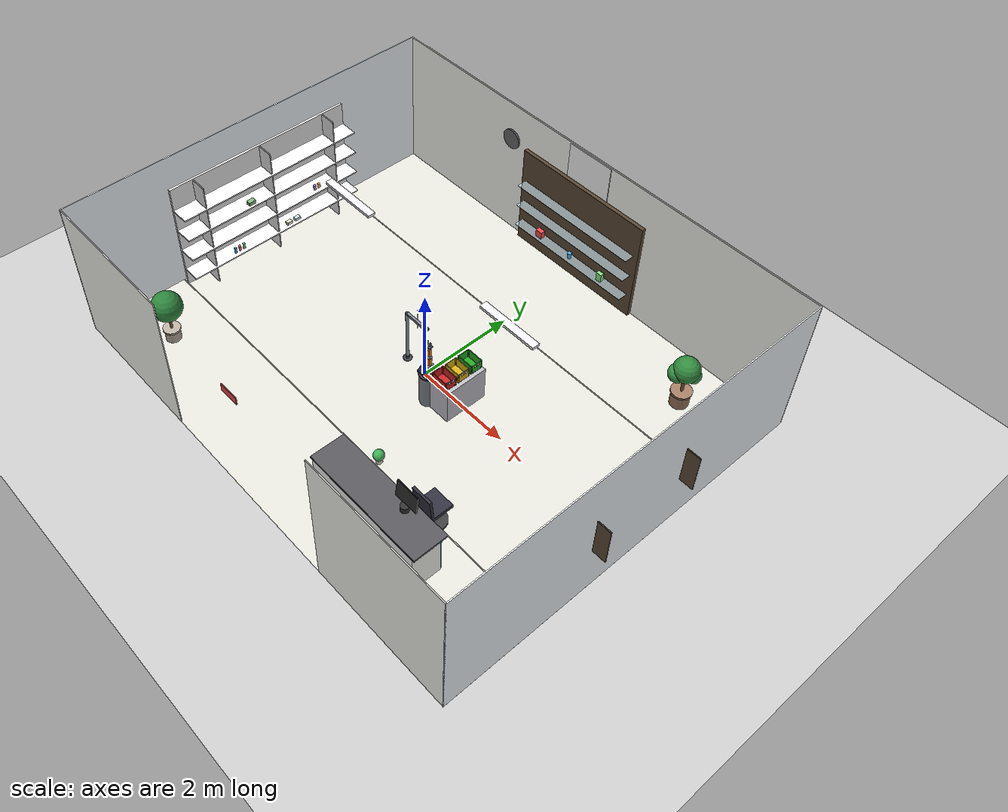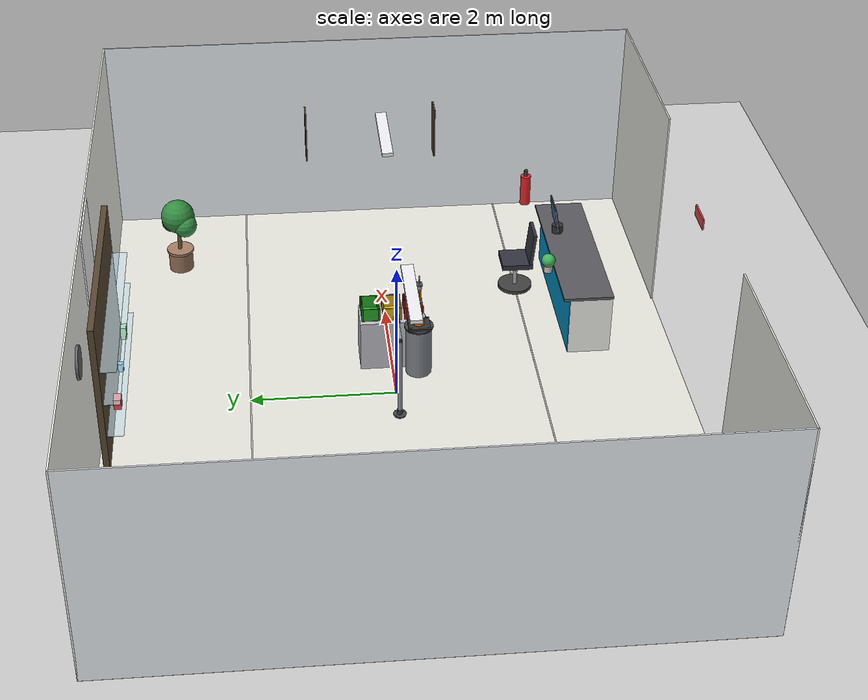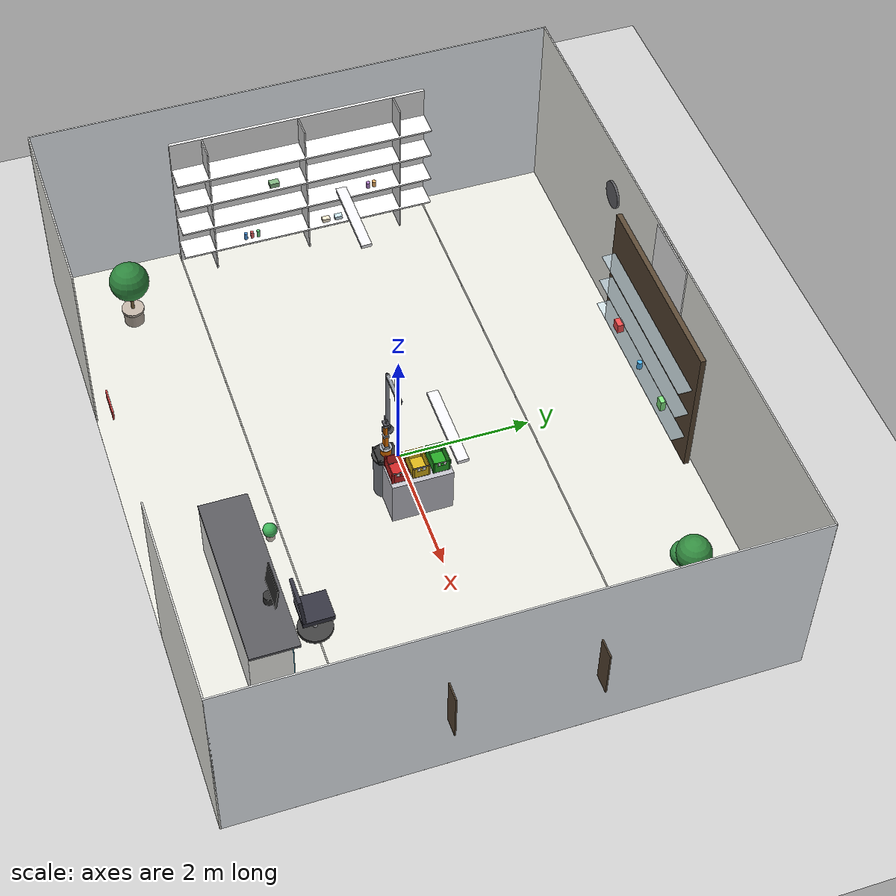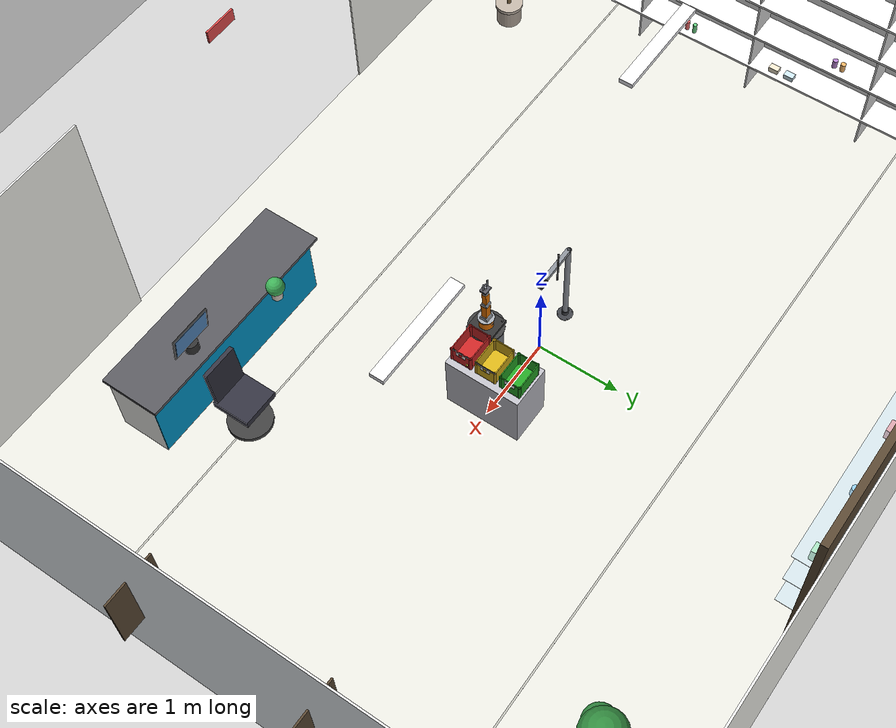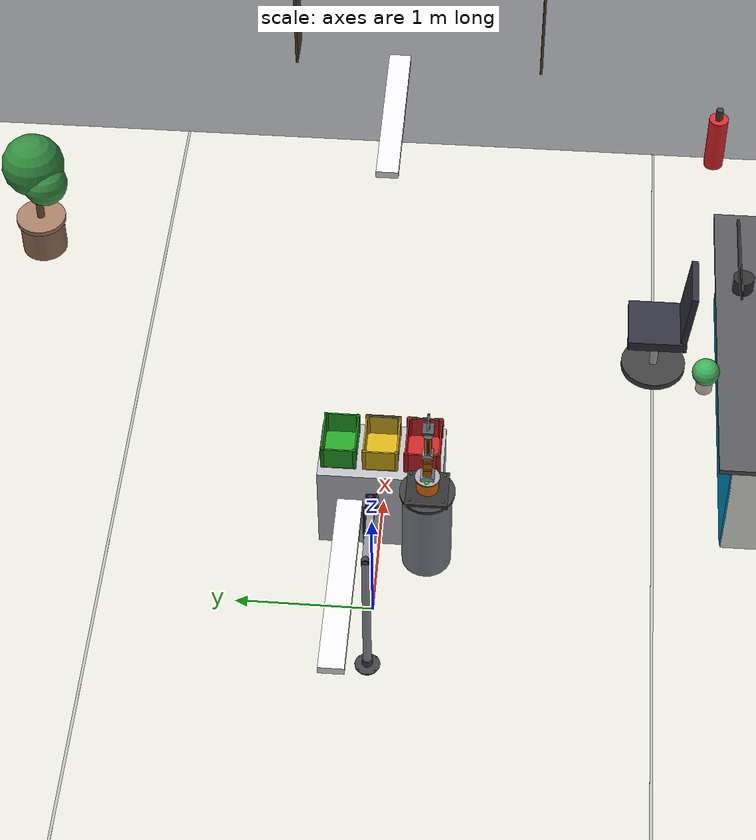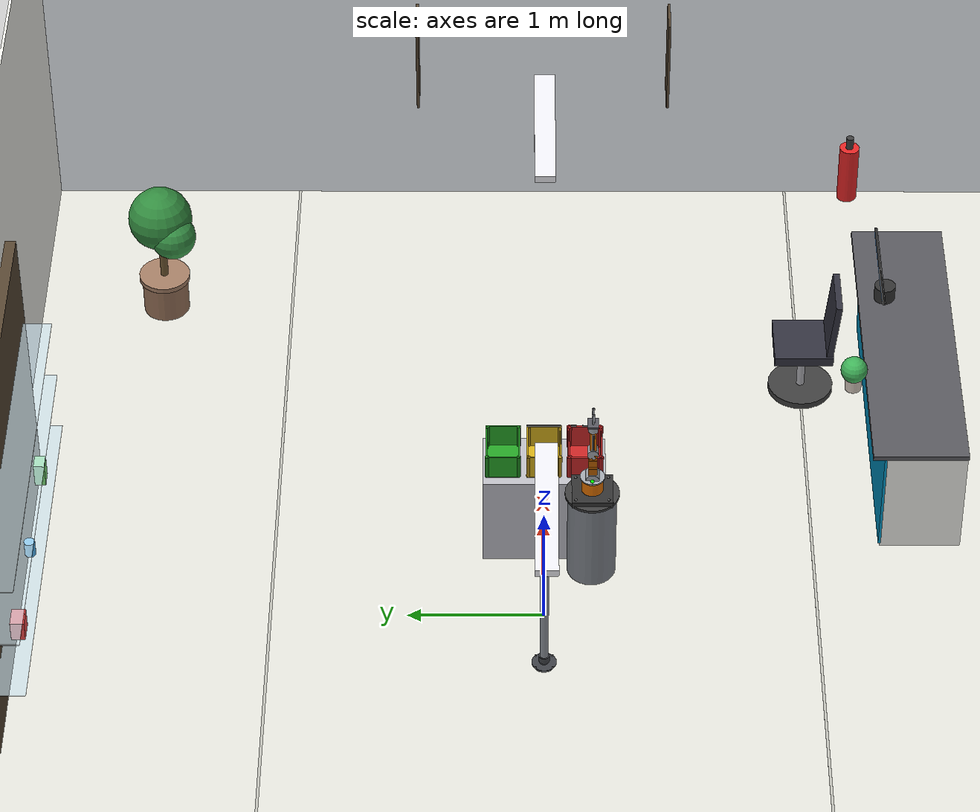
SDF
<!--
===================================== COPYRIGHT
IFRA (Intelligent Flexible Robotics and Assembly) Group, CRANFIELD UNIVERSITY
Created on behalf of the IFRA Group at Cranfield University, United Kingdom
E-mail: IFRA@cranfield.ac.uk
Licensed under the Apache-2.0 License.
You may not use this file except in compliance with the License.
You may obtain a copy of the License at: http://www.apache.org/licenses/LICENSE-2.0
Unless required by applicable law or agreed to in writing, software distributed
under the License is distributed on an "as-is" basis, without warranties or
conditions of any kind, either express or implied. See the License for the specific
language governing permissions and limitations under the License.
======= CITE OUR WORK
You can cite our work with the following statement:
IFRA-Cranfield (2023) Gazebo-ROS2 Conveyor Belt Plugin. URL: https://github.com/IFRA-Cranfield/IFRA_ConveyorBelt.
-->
<sdf version="1.4">
 <world name="default">
  <gravity>0 0 -9.8</gravity>
  <include><uri>model://ground_plane</uri></include>
  <include><uri>model://sun</uri></include>
  <scene>
   <ambient>0.45 0.47 0.50 1</ambient>
   <background>0.96 0.98 1.00 1</background>
   <shadows>1</shadows>
  </scene>
  <light name="pharmacy_overhead_fill" type="point">
   <pose>0 0 2.9 0 0 0</pose>
   <diffuse>0.95 0.98 1.0 1</diffuse>
   <specular>0.2 0.2 0.2 1</specular>
   <attenuation>
    <range>12</range>
    <constant>0.6</constant>
    <linear>0.02</linear>
    <quadratic>0.001</quadratic>
   </attenuation>
  </light>
  <light name="pharmacy_panel_1" type="point">
   <pose>-1.5 -1.5 2.9 0 0 0</pose>
   <diffuse>0.90 0.95 1.0 1</diffuse>
   <specular>0.15 0.15 0.15 1</specular>
   <attenuation>
    <range>10</range>
    <constant>0.7</constant>
    <linear>0.03</linear>
    <quadratic>0.002</quadratic>
   </attenuation>
  </light>
  <light name="pharmacy_panel_2" type="point">
   <pose>1.5 -1.5 2.9 0 0 0</pose>
   <diffuse>0.90 0.95 1.0 1</diffuse>
   <specular>0.15 0.15 0.15 1</specular>
   <attenuation>
    <range>10</range>
    <constant>0.7</constant>
    <linear>0.03</linear>
    <quadratic>0.002</quadratic>
   </attenuation>
  </light>
  <light name="pharmacy_panel_3" type="point">
   <pose>-1.5 1.5 2.9 0 0 0</pose>
   <diffuse>0.90 0.95 1.0 1</diffuse>
   <specular>0.15 0.15 0.15 1</specular>
   <attenuation>
    <range>10</range>
    <constant>0.7</constant>
    <linear>0.03</linear>
    <quadratic>0.002</quadratic>
   </attenuation>
  </light>
  <light name="pharmacy_panel_4" type="point">
   <pose>1.5 1.5 2.9 0 0 0</pose>
   <diffuse>0.90 0.95 1.0 1</diffuse>
   <specular>0.15 0.15 0.15 1</specular>
   <attenuation>
    <range>10</range>
    <constant>0.7</constant>
    <linear>0.03</linear>
    <quadratic>0.002</quadratic>
   </attenuation>
  </light>
  <light name="conveyor_spot" type="spot">
   <pose>0 0 2.8 0 0 0</pose>
   <diffuse>1 1 1 1</diffuse>
   <specular>0.2 0.2 0.2 1</specular>
   <direction>0 0 -1</direction>
   <spot><inner_angle>0.5</inner_angle><outer_angle>0.9</outer_angle><falloff>0.8</falloff></spot>
   <attenuation>
    <range>8</range>
    <constant>0.7</constant>
    <linear>0.02</linear>
    <quadratic>0.004</quadratic>
   </attenuation>
  </light>
  <plugin name="gazebo_ros_init" filename="libgazebo_ros_init.so"><ros><namespace>/</namespace></ros></plugin>
  <plugin name="gazebo_ros_factory" filename="libgazebo_ros_factory.so">
   <ros><namespace>/</namespace></ros>
  </plugin>
  <plugin name="gazebo_ros_state" filename="libgazebo_ros_state.so"><ros><namespace>/</namespace></ros></plugin>
  <include><name>pharmacy_environment</name><uri>model://pharmacy_environment</uri></include>
  <include><name>scanner_arm</name><pose>-0.5 0 0 0 0 0</pose><uri>model://scanner_arm</uri></include>
  <include>
   <name>sorting_robot_arm</name>
   <pose>0.5 -0.35 0.75 0 0 1.5708</pose>
   <uri>model://sorting_robot_arm</uri>
  </include>
  <include><name>bin_valid</name><pose>0.85 0.30 0.75 0 0 0</pose><uri>model://sorting_bin_valid</uri></include>
  <include>
   <name>bin_expired</name>
   <pose>0.85 0.0 0.75 0 0 0</pose>
   <uri>model://sorting_bin_expired</uri>
  </include>
  <include>
   <name>bin_counterfeit</name>
   <pose>0.85 -0.30 0.75 0 0 0</pose>
   <uri>model://sorting_bin_counterfeit</uri>
  </include>
  <model name="bin_stand">
   <static>true</static>
   <pose>0.85 0.0 0.375 0 0 0</pose>
   <link name="stand_link">
    <collision name="stand_collision"><geometry><box><size>0.50 0.90 0.75</size></box></geometry></collision>
    <visual name="stand_visual">
     <geometry><box><size>0.50 0.90 0.75</size></box></geometry>
     <material>
      <ambient>0.6 0.6 0.62 1</ambient>
      <diffuse>0.75 0.75 0.78 1</diffuse>
      <specular>0.3 0.3 0.3 1</specular>
     </material>
    </visual>
    <visual name="leg_fl">
     <pose>0.22 0.42 -0.30 0 0 0</pose>
     <geometry><cylinder><radius>0.025</radius><length>0.15</length></cylinder></geometry>
     <material><ambient>0.3 0.3 0.3 1</ambient><diffuse>0.4 0.4 0.4 1</diffuse></material>
    </visual>
    <visual name="leg_fr">
     <pose>0.22 -0.42 -0.30 0 0 0</pose>
     <geometry><cylinder><radius>0.025</radius><length>0.15</length></cylinder></geometry>
     <material><ambient>0.3 0.3 0.3 1</ambient><diffuse>0.4 0.4 0.4 1</diffuse></material>
    </visual>
    <visual name="leg_bl">
     <pose>-0.22 0.42 -0.30 0 0 0</pose>
     <geometry><cylinder><radius>0.025</radius><length>0.15</length></cylinder></geometry>
     <material><ambient>0.3 0.3 0.3 1</ambient><diffuse>0.4 0.4 0.4 1</diffuse></material>
    </visual>
    <visual name="leg_br">
     <pose>-0.22 -0.42 -0.30 0 0 0</pose>
     <geometry><cylinder><radius>0.025</radius><length>0.15</length></cylinder></geometry>
     <material><ambient>0.3 0.3 0.3 1</ambient><diffuse>0.4 0.4 0.4 1</diffuse></material>
    </visual>
   </link>
  </model>
  <model name="robot_pedestal">
   <static>true</static>
   <pose>0.5 -0.35 0.375 0 0 0</pose>
   <link name="pedestal_link">
    <collision name="pedestal_collision">
     <geometry><cylinder><radius>0.18</radius><length>0.75</length></cylinder></geometry>
    </collision>
    <visual name="pedestal_visual">
     <geometry><cylinder><radius>0.18</radius><length>0.75</length></cylinder></geometry>
     <material>
      <ambient>0.4 0.42 0.45 1</ambient>
      <diffuse>0.5 0.52 0.55 1</diffuse>
      <specular>0.4 0.4 0.4 1</specular>
     </material>
    </visual>
    <visual name="mounting_plate">
     <pose>0 0 0.38 0 0 0</pose>
     <geometry><cylinder><radius>0.20</radius><length>0.02</length></cylinder></geometry>
     <material>
      <ambient>0.2 0.2 0.2 1</ambient>
      <diffuse>0.25 0.25 0.25 1</diffuse>
      <specular>0.6 0.6 0.6 1</specular>
     </material>
    </visual>
   </link>
  </model>
 </world>
</sdf>

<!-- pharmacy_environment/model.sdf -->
<sdf version="1.6">
  <model name="pharmacy_environment">
    <static>true</static>

    <link name="room">
      <!-- ==================== FLOOR ==================== -->
      <visual name="floor_visual">
        <pose>0 0 0.001 0 0 0</pose>
        <geometry>
          <box><size>10 8 0.002</size></box>
        </geometry>
        <material>
          <ambient>0.85 0.85 0.82 1</ambient>
          <diffuse>0.9 0.9 0.87 1</diffuse>
          <specular>0.3 0.3 0.3 1</specular>
        </material>
      </visual>
      <!-- Floor tiles pattern -->
      <visual name="floor_tile_line1">
        <pose>0 -2 0.002 0 0 0</pose>
        <geometry><box><size>10 0.02 0.001</size></box></geometry>
        <material><ambient>0.7 0.7 0.68 1</ambient><diffuse>0.75 0.75 0.72 1</diffuse></material>
      </visual>
      <visual name="floor_tile_line2">
        <pose>0 2 0.002 0 0 0</pose>
        <geometry><box><size>10 0.02 0.001</size></box></geometry>
        <material><ambient>0.7 0.7 0.68 1</ambient><diffuse>0.75 0.75 0.72 1</diffuse></material>
      </visual>

      <!-- ==================== WALLS ==================== -->
      <!-- Back wall with nice color -->
      <visual name="back_wall">
        <pose>0 3.99 1.5 0 0 0</pose>
        <geometry><box><size>10 0.02 3</size></box></geometry>
        <material>
          <ambient>0.95 0.95 0.92 1</ambient>
          <diffuse>0.98 0.98 0.95 1</diffuse>
          <specular>0.1 0.1 0.1 1</specular>
        </material>
      </visual>
      <!-- Front wall (partial, with opening) -->
      <visual name="front_wall_left">
        <pose>-3.5 -3.99 1.5 0 0 0</pose>
        <geometry><box><size>3 0.02 3</size></box></geometry>
        <material>
          <ambient>0.95 0.95 0.92 1</ambient>
          <diffuse>0.98 0.98 0.95 1</diffuse>
        </material>
      </visual>
      <visual name="front_wall_right">
        <pose>3.5 -3.99 1.5 0 0 0</pose>
        <geometry><box><size>3 0.02 3</size></box></geometry>
        <material>
          <ambient>0.95 0.95 0.92 1</ambient>
          <diffuse>0.98 0.98 0.95 1</diffuse>
        </material>
      </visual>
      <!-- Side walls -->
      <visual name="left_wall">
        <pose>-4.99 0 1.5 0 0 0</pose>
        <geometry><box><size>0.02 8 3</size></box></geometry>
        <material>
          <ambient>0.92 0.94 0.96 1</ambient>
          <diffuse>0.95 0.97 0.99 1</diffuse>
        </material>
      </visual>
      <visual name="right_wall">
        <pose>4.99 0 1.5 0 0 0</pose>
        <geometry><box><size>0.02 8 3</size></box></geometry>
        <material>
          <ambient>0.92 0.94 0.96 1</ambient>
          <diffuse>0.95 0.97 0.99 1</diffuse>
        </material>
      </visual>

      <!-- ==================== MODERN PHARMACY SHELVING UNIT (Left Wall) ==================== -->
      <!-- Main shelf frame -->
      <visual name="shelf_unit_back">
        <pose>-4.85 0 1.2 0 0 0</pose>
        <geometry><box><size>0.05 4.0 2.4</size></box></geometry>
        <material><ambient>0.85 0.85 0.85 1</ambient><diffuse>0.9 0.9 0.9 1</diffuse><specular>0.2 0.2 0.2 1</specular></material>
      </visual>
      <!-- Shelf levels -->
      <visual name="shelf_l1">
        <pose>-4.65 0 0.4 0 0 0</pose>
        <geometry><box><size>0.4 4.0 0.025</size></box></geometry>
        <material><ambient>0.95 0.95 0.95 1</ambient><diffuse>0.98 0.98 0.98 1</diffuse><specular>0.3 0.3 0.3 1</specular></material>
      </visual>
      <visual name="shelf_l2">
        <pose>-4.65 0 0.9 0 0 0</pose>
        <geometry><box><size>0.4 4.0 0.025</size></box></geometry>
        <material><ambient>0.95 0.95 0.95 1</ambient><diffuse>0.98 0.98 0.98 1</diffuse><specular>0.3 0.3 0.3 1</specular></material>
      </visual>
      <visual name="shelf_l3">
        <pose>-4.65 0 1.4 0 0 0</pose>
        <geometry><box><size>0.4 4.0 0.025</size></box></geometry>
        <material><ambient>0.95 0.95 0.95 1</ambient><diffuse>0.98 0.98 0.98 1</diffuse><specular>0.3 0.3 0.3 1</specular></material>
      </visual>
      <visual name="shelf_l4">
        <pose>-4.65 0 1.9 0 0 0</pose>
        <geometry><box><size>0.4 4.0 0.025</size></box></geometry>
        <material><ambient>0.95 0.95 0.95 1</ambient><diffuse>0.98 0.98 0.98 1</diffuse><specular>0.3 0.3 0.3 1</specular></material>
      </visual>
      <!-- Vertical dividers -->
      <visual name="shelf_div1">
        <pose>-4.65 -1.5 1.2 0 0 0</pose>
        <geometry><box><size>0.35 0.02 2.4</size></box></geometry>
        <material><ambient>0.8 0.8 0.8 1</ambient><diffuse>0.85 0.85 0.85 1</diffuse></material>
      </visual>
      <visual name="shelf_div2">
        <pose>-4.65 0 1.2 0 0 0</pose>
        <geometry><box><size>0.35 0.02 2.4</size></box></geometry>
        <material><ambient>0.8 0.8 0.8 1</ambient><diffuse>0.85 0.85 0.85 1</diffuse></material>
      </visual>
      <visual name="shelf_div3">
        <pose>-4.65 1.5 1.2 0 0 0</pose>
        <geometry><box><size>0.35 0.02 2.4</size></box></geometry>
        <material><ambient>0.8 0.8 0.8 1</ambient><diffuse>0.85 0.85 0.85 1</diffuse></material>
      </visual>

      <!-- Medicine bottles on shelves (colorful) -->
      <visual name="med_bottle_1"><pose>-4.55 -1.0 0.48 0 0 0</pose><geometry><cylinder><radius>0.025</radius><length>0.12</length></cylinder></geometry><material><ambient>0.2 0.5 0.8 1</ambient><diffuse>0.3 0.6 0.9 1</diffuse></material></visual>
      <visual name="med_bottle_2"><pose>-4.55 -0.9 0.48 0 0 0</pose><geometry><cylinder><radius>0.025</radius><length>0.12</length></cylinder></geometry><material><ambient>0.8 0.3 0.3 1</ambient><diffuse>0.9 0.4 0.4 1</diffuse></material></visual>
      <visual name="med_bottle_3"><pose>-4.55 -0.8 0.48 0 0 0</pose><geometry><cylinder><radius>0.025</radius><length>0.12</length></cylinder></geometry><material><ambient>0.3 0.7 0.4 1</ambient><diffuse>0.4 0.8 0.5 1</diffuse></material></visual>
      <visual name="med_box_1"><pose>-4.55 0.3 0.45 0 0 0</pose><geometry><box><size>0.08 0.12 0.06</size></box></geometry><material><ambient>0.9 0.85 0.7 1</ambient><diffuse>0.95 0.9 0.8 1</diffuse></material></visual>
      <visual name="med_box_2"><pose>-4.55 0.5 0.45 0 0 0</pose><geometry><box><size>0.08 0.12 0.06</size></box></geometry><material><ambient>0.7 0.85 0.9 1</ambient><diffuse>0.8 0.9 0.95 1</diffuse></material></visual>
      <visual name="med_bottle_4"><pose>-4.55 1.0 0.98 0 0 0</pose><geometry><cylinder><radius>0.03</radius><length>0.1</length></cylinder></geometry><material><ambient>0.6 0.4 0.7 1</ambient><diffuse>0.7 0.5 0.8 1</diffuse></material></visual>
      <visual name="med_bottle_5"><pose>-4.55 1.1 0.98 0 0 0</pose><geometry><cylinder><radius>0.03</radius><length>0.1</length></cylinder></geometry><material><ambient>0.9 0.6 0.3 1</ambient><diffuse>0.95 0.7 0.4 1</diffuse></material></visual>
      <visual name="med_box_3"><pose>-4.55 -0.5 1.45 0 0 0</pose><geometry><box><size>0.1 0.15 0.08</size></box></geometry><material><ambient>0.4 0.6 0.4 1</ambient><diffuse>0.5 0.7 0.5 1</diffuse></material></visual>

      <!-- ==================== BACK WALL DISPLAY CABINET ==================== -->
      <visual name="cabinet_frame">
        <pose>0 3.85 1.2 0 0 0</pose>
        <geometry><box><size>3.0 0.08 2.2</size></box></geometry>
        <material><ambient>0.25 0.2 0.15 1</ambient><diffuse>0.35 0.28 0.2 1</diffuse><specular>0.4 0.4 0.4 1</specular></material>
      </visual>
      <!-- Glass shelves -->
      <visual name="cabinet_shelf1">
        <pose>0 3.75 0.6 0 0 0</pose>
        <geometry><box><size>2.8 0.3 0.01</size></box></geometry>
        <material><ambient>0.7 0.8 0.85 0.5</ambient><diffuse>0.8 0.9 0.95 0.6</diffuse><specular>0.9 0.9 0.9 1</specular></material>
      </visual>
      <visual name="cabinet_shelf2">
        <pose>0 3.75 1.1 0 0 0</pose>
        <geometry><box><size>2.8 0.3 0.01</size></box></geometry>
        <material><ambient>0.7 0.8 0.85 0.5</ambient><diffuse>0.8 0.9 0.95 0.6</diffuse><specular>0.9 0.9 0.9 1</specular></material>
      </visual>
      <visual name="cabinet_shelf3">
        <pose>0 3.75 1.6 0 0 0</pose>
        <geometry><box><size>2.8 0.3 0.01</size></box></geometry>
        <material><ambient>0.7 0.8 0.85 0.5</ambient><diffuse>0.8 0.9 0.95 0.6</diffuse><specular>0.9 0.9 0.9 1</specular></material>
      </visual>
      <!-- Display items -->
      <visual name="display_1"><pose>-0.8 3.7 0.7 0 0 0</pose><geometry><box><size>0.15 0.1 0.15</size></box></geometry><material><ambient>0.9 0.2 0.2 1</ambient><diffuse>0.95 0.3 0.3 1</diffuse></material></visual>
      <visual name="display_2"><pose>0 3.7 0.68 0 0 0</pose><geometry><cylinder><radius>0.04</radius><length>0.12</length></cylinder></geometry><material><ambient>0.2 0.6 0.9 1</ambient><diffuse>0.3 0.7 0.95 1</diffuse></material></visual>
      <visual name="display_3"><pose>0.8 3.7 0.7 0 0 0</pose><geometry><box><size>0.12 0.08 0.18</size></box></geometry><material><ambient>0.4 0.8 0.4 1</ambient><diffuse>0.5 0.9 0.5 1</diffuse></material></visual>

      <!-- ==================== PHARMACY CROSS SIGN (Glowing Green) ==================== -->
      <visual name="cross_h">
        <pose>0 3.97 2.5 0 0 0</pose>
        <geometry><box><size>0.8 0.03 0.2</size></box></geometry>
        <material><ambient>0.0 0.8 0.3 1</ambient><diffuse>0.0 0.9 0.4 1</diffuse><emissive>0.0 0.6 0.2 1</emissive></material>
      </visual>
      <visual name="cross_v">
        <pose>0 3.97 2.5 0 0 0</pose>
        <geometry><box><size>0.2 0.03 0.8</size></box></geometry>
        <material><ambient>0.0 0.8 0.3 1</ambient><diffuse>0.0 0.9 0.4 1</diffuse><emissive>0.0 0.6 0.2 1</emissive></material>
      </visual>
      <visual name="cross_backing">
        <pose>0 3.96 2.5 0 0 0</pose>
        <geometry><box><size>1.0 0.02 1.0</size></box></geometry>
        <material><ambient>0.95 0.95 0.95 1</ambient><diffuse>0.98 0.98 0.98 1</diffuse></material>
      </visual>

      <!-- ==================== DECORATIVE POTTED PLANTS ==================== -->
      <!-- Large floor plant 1 -->
      <visual name="pot1_base">
        <pose>3.5 3.0 0.15 0 0 0</pose>
        <geometry><cylinder><radius>0.18</radius><length>0.3</length></cylinder></geometry>
        <material><ambient>0.5 0.35 0.25 1</ambient><diffuse>0.6 0.45 0.35 1</diffuse></material>
      </visual>
      <visual name="pot1_rim">
        <pose>3.5 3.0 0.32 0 0 0</pose>
        <geometry><cylinder><radius>0.2</radius><length>0.04</length></cylinder></geometry>
        <material><ambient>0.55 0.4 0.3 1</ambient><diffuse>0.65 0.5 0.4 1</diffuse></material>
      </visual>
      <visual name="pot1_soil">
        <pose>3.5 3.0 0.28 0 0 0</pose>
        <geometry><cylinder><radius>0.16</radius><length>0.02</length></cylinder></geometry>
        <material><ambient>0.25 0.18 0.12 1</ambient><diffuse>0.3 0.22 0.15 1</diffuse></material>
      </visual>
      <visual name="plant1_trunk">
        <pose>3.5 3.0 0.55 0 0 0</pose>
        <geometry><cylinder><radius>0.03</radius><length>0.5</length></cylinder></geometry>
        <material><ambient>0.35 0.25 0.15 1</ambient><diffuse>0.45 0.35 0.2 1</diffuse></material>
      </visual>
      <visual name="plant1_leaves1">
        <pose>3.5 3.0 0.9 0 0 0</pose>
        <geometry><sphere><radius>0.25</radius></sphere></geometry>
        <material><ambient>0.15 0.45 0.2 1</ambient><diffuse>0.2 0.55 0.25 1</diffuse></material>
      </visual>
      <visual name="plant1_leaves2">
        <pose>3.6 3.1 0.75 0 0 0</pose>
        <geometry><sphere><radius>0.15</radius></sphere></geometry>
        <material><ambient>0.2 0.5 0.25 1</ambient><diffuse>0.25 0.6 0.3 1</diffuse></material>
      </visual>
      <visual name="plant1_leaves3">
        <pose>3.4 2.9 0.8 0 0 0</pose>
        <geometry><sphere><radius>0.18</radius></sphere></geometry>
        <material><ambient>0.18 0.48 0.22 1</ambient><diffuse>0.22 0.58 0.28 1</diffuse></material>
      </visual>

      <!-- Large floor plant 2 -->
      <visual name="pot2_base">
        <pose>-3.8 -3.0 0.12 0 0 0</pose>
        <geometry><cylinder><radius>0.15</radius><length>0.24</length></cylinder></geometry>
        <material><ambient>0.6 0.55 0.5 1</ambient><diffuse>0.7 0.65 0.6 1</diffuse></material>
      </visual>
      <visual name="pot2_rim">
        <pose>-3.8 -3.0 0.26 0 0 0</pose>
        <geometry><cylinder><radius>0.17</radius><length>0.04</length></cylinder></geometry>
        <material><ambient>0.65 0.6 0.55 1</ambient><diffuse>0.75 0.7 0.65 1</diffuse></material>
      </visual>
      <visual name="plant2_trunk">
        <pose>-3.8 -3.0 0.5 0 0 0</pose>
        <geometry><cylinder><radius>0.025</radius><length>0.45</length></cylinder></geometry>
        <material><ambient>0.4 0.3 0.2 1</ambient><diffuse>0.5 0.4 0.25 1</diffuse></material>
      </visual>
      <visual name="plant2_foliage">
        <pose>-3.8 -3.0 0.85 0 0 0</pose>
        <geometry><sphere><radius>0.3</radius></sphere></geometry>
        <material><ambient>0.12 0.42 0.18 1</ambient><diffuse>0.18 0.52 0.24 1</diffuse></material>
      </visual>

      <!-- Small desk plant -->
      <visual name="pot3">
        <pose>1.5 -2.3 0.95 0 0 0</pose>
        <geometry><cylinder><radius>0.06</radius><length>0.1</length></cylinder></geometry>
        <material><ambient>0.8 0.75 0.7 1</ambient><diffuse>0.85 0.8 0.75 1</diffuse></material>
      </visual>
      <visual name="plant3_leaves">
        <pose>1.5 -2.3 1.08 0 0 0</pose>
        <geometry><sphere><radius>0.1</radius></sphere></geometry>
        <material><ambient>0.2 0.6 0.3 1</ambient><diffuse>0.25 0.7 0.35 1</diffuse></material>
      </visual>

      <!-- ==================== MODERN RECEPTION COUNTER ==================== -->
      <visual name="counter_main">
        <pose>2.0 -2.8 0.45 0 0 0</pose>
        <geometry><box><size>2.5 0.6 0.9</size></box></geometry>
        <material><ambient>0.92 0.92 0.9 1</ambient><diffuse>0.96 0.96 0.94 1</diffuse><specular>0.2 0.2 0.2 1</specular></material>
      </visual>
      <visual name="counter_top">
        <pose>2.0 -2.75 0.92 0 0 0</pose>
        <geometry><box><size>2.6 0.7 0.04</size></box></geometry>
        <material><ambient>0.3 0.3 0.32 1</ambient><diffuse>0.35 0.35 0.37 1</diffuse><specular>0.6 0.6 0.6 1</specular></material>
      </visual>
      <visual name="counter_accent">
        <pose>2.0 -2.5 0.45 0 0 0</pose>
        <geometry><box><size>2.5 0.02 0.85</size></box></geometry>
        <material><ambient>0.0 0.5 0.7 1</ambient><diffuse>0.0 0.6 0.8 1</diffuse></material>
      </visual>
      <!-- Computer monitor on counter -->
      <visual name="monitor_stand">
        <pose>2.5 -2.6 1.0 0 0 0</pose>
        <geometry><cylinder><radius>0.08</radius><length>0.12</length></cylinder></geometry>
        <material><ambient>0.15 0.15 0.15 1</ambient><diffuse>0.2 0.2 0.2 1</diffuse></material>
      </visual>
      <visual name="monitor_screen">
        <pose>2.5 -2.55 1.25 -0.15 0 0</pose>
        <geometry><box><size>0.5 0.02 0.35</size></box></geometry>
        <material><ambient>0.1 0.1 0.1 1</ambient><diffuse>0.15 0.15 0.15 1</diffuse><specular>0.8 0.8 0.8 1</specular></material>
      </visual>
      <visual name="monitor_display">
        <pose>2.5 -2.54 1.25 -0.15 0 0</pose>
        <geometry><box><size>0.46 0.01 0.31</size></box></geometry>
        <material><ambient>0.2 0.4 0.6 1</ambient><diffuse>0.3 0.5 0.7 1</diffuse><emissive>0.1 0.2 0.3 1</emissive></material>
      </visual>

      <!-- ==================== OFFICE CHAIR ==================== -->
      <visual name="chair_base">
        <pose>2.5 -2.0 0.05 0 0 0</pose>
        <geometry><cylinder><radius>0.25</radius><length>0.05</length></cylinder></geometry>
        <material><ambient>0.2 0.2 0.2 1</ambient><diffuse>0.25 0.25 0.25 1</diffuse></material>
      </visual>
      <visual name="chair_pole">
        <pose>2.5 -2.0 0.25 0 0 0</pose>
        <geometry><cylinder><radius>0.03</radius><length>0.35</length></cylinder></geometry>
        <material><ambient>0.6 0.6 0.62 1</ambient><diffuse>0.7 0.7 0.72 1</diffuse><specular>0.5 0.5 0.5 1</specular></material>
      </visual>
      <visual name="chair_seat">
        <pose>2.5 -2.0 0.48 0 0 0</pose>
        <geometry><box><size>0.45 0.45 0.08</size></box></geometry>
        <material><ambient>0.15 0.15 0.18 1</ambient><diffuse>0.2 0.2 0.25 1</diffuse></material>
      </visual>
      <visual name="chair_back">
        <pose>2.5 -2.22 0.75 0.1 0 0</pose>
        <geometry><box><size>0.42 0.05 0.5</size></box></geometry>
        <material><ambient>0.15 0.15 0.18 1</ambient><diffuse>0.2 0.2 0.25 1</diffuse></material>
      </visual>

      <!-- ==================== WALL CLOCK ==================== -->
      <visual name="clock_body">
        <pose>-2.0 3.97 2.2 1.5708 0 0</pose>
        <geometry><cylinder><radius>0.2</radius><length>0.04</length></cylinder></geometry>
        <material><ambient>0.9 0.9 0.9 1</ambient><diffuse>0.95 0.95 0.95 1</diffuse><specular>0.3 0.3 0.3 1</specular></material>
      </visual>
      <visual name="clock_face">
        <pose>-2.0 3.96 2.2 1.5708 0 0</pose>
        <geometry><cylinder><radius>0.18</radius><length>0.01</length></cylinder></geometry>
        <material><ambient>1 1 1 1</ambient><diffuse>1 1 1 1</diffuse></material>
      </visual>
      <visual name="clock_frame">
        <pose>-2.0 3.97 2.2 1.5708 0 0</pose>
        <geometry><cylinder><radius>0.21</radius><length>0.05</length></cylinder></geometry>
        <material><ambient>0.3 0.3 0.32 1</ambient><diffuse>0.4 0.4 0.42 1</diffuse></material>
      </visual>

      <!-- ==================== INFORMATIONAL POSTERS ==================== -->
      <visual name="poster1_frame">
        <pose>4.97 1.0 1.5 0 0 1.5708</pose>
        <geometry><box><size>0.02 0.6 0.8</size></box></geometry>
        <material><ambient>0.25 0.2 0.15 1</ambient><diffuse>0.35 0.28 0.2 1</diffuse></material>
      </visual>
      <visual name="poster1">
        <pose>4.96 1.0 1.5 0 0 1.5708</pose>
        <geometry><box><size>0.01 0.55 0.75</size></box></geometry>
        <material><ambient>0.85 0.9 0.95 1</ambient><diffuse>0.9 0.95 1.0 1</diffuse></material>
      </visual>
      <visual name="poster2_frame">
        <pose>4.97 -1.0 1.5 0 0 1.5708</pose>
        <geometry><box><size>0.02 0.6 0.8</size></box></geometry>
        <material><ambient>0.25 0.2 0.15 1</ambient><diffuse>0.35 0.28 0.2 1</diffuse></material>
      </visual>
      <visual name="poster2">
        <pose>4.96 -1.0 1.5 0 0 1.5708</pose>
        <geometry><box><size>0.01 0.55 0.75</size></box></geometry>
        <material><ambient>0.95 0.9 0.85 1</ambient><diffuse>1.0 0.95 0.9 1</diffuse></material>
      </visual>

      <!-- ==================== CEILING LIGHTS ==================== -->
      <visual name="light_fixture1">
        <pose>-2 0 2.95 0 0 0</pose>
        <geometry><box><size>1.2 0.15 0.05</size></box></geometry>
        <material><ambient>0.9 0.9 0.92 1</ambient><diffuse>0.95 0.95 0.97 1</diffuse><emissive>0.8 0.8 0.85 1</emissive></material>
      </visual>
      <visual name="light_fixture2">
        <pose>2 0 2.95 0 0 0</pose>
        <geometry><box><size>1.2 0.15 0.05</size></box></geometry>
        <material><ambient>0.9 0.9 0.92 1</ambient><diffuse>0.95 0.95 0.97 1</diffuse><emissive>0.8 0.8 0.85 1</emissive></material>
      </visual>

      <!-- ==================== EXIT SIGN ==================== -->
      <visual name="exit_sign">
        <pose>0 -3.97 2.6 0 0 0</pose>
        <geometry><box><size>0.4 0.02 0.15</size></box></geometry>
        <material><ambient>0.8 0.2 0.2 1</ambient><diffuse>0.9 0.3 0.3 1</diffuse><emissive>0.5 0.1 0.1 1</emissive></material>
      </visual>

      <!-- ==================== SAFETY EQUIPMENT ==================== -->
      <!-- Fire extinguisher -->
      <visual name="extinguisher_body">
        <pose>4.8 -2.5 0.35 0 0 0</pose>
        <geometry><cylinder><radius>0.08</radius><length>0.5</length></cylinder></geometry>
        <material><ambient>0.8 0.1 0.1 1</ambient><diffuse>0.9 0.15 0.15 1</diffuse></material>
      </visual>
      <visual name="extinguisher_top">
        <pose>4.8 -2.5 0.65 0 0 0</pose>
        <geometry><cylinder><radius>0.03</radius><length>0.1</length></cylinder></geometry>
        <material><ambient>0.2 0.2 0.2 1</ambient><diffuse>0.25 0.25 0.25 1</diffuse></material>
      </visual>

    </link>
  </model>
</sdf>

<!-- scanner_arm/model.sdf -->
<!--
  Scanner arm model (SDF) for Gazebo Classic.
  - Vertical pole with horizontal extension.
  - Downward-facing camera sensor.
  - Static model.
-->
<sdf version="1.6">
  <model name="scanner_arm">
    <static>true</static>

    <link name="base_plate">
      <pose>0 0 0.01 0 0 0</pose>
      <inertial>
        <mass>5.0</mass>
        <inertia>
          <ixx>0.02</ixx>
          <ixy>0</ixy>
          <ixz>0</ixz>
          <iyy>0.02</iyy>
          <iyz>0</iyz>
          <izz>0.01</izz>
        </inertia>
      </inertial>
      <collision name="base_collision">
        <geometry>
          <cylinder>
            <radius>0.08</radius>
            <length>0.02</length>
          </cylinder>
        </geometry>
      </collision>
      <visual name="base_visual">
        <geometry>
          <cylinder>
            <radius>0.08</radius>
            <length>0.02</length>
          </cylinder>
        </geometry>
        <material>
          <ambient>0.55 0.57 0.60 1</ambient>
          <diffuse>0.55 0.57 0.60 1</diffuse>
          <specular>0.9 0.9 0.9 1</specular>
          <pbr>
            <metal>
              <albedo>0.55 0.57 0.60 1</albedo>
              <metalness>1.0</metalness>
              <roughness>0.2</roughness>
            </metal>
          </pbr>
        </material>
      </visual>

      <!-- Decorative flange ring + bolts (visual only) -->
      <visual name="base_ring_visual">
        <pose>0 0 0.015 0 0 0</pose>
        <geometry>
          <cylinder>
            <radius>0.09</radius>
            <length>0.005</length>
          </cylinder>
        </geometry>
        <material>
          <ambient>0.25 0.26 0.28 1</ambient>
          <diffuse>0.25 0.26 0.28 1</diffuse>
          <specular>0.6 0.6 0.6 1</specular>
        </material>
      </visual>
      <visual name="bolt_1">
        <pose>0.06 0.06 0.02 0 0 0</pose>
        <geometry>
          <cylinder>
            <radius>0.006</radius>
            <length>0.01</length>
          </cylinder>
        </geometry>
        <material>
          <ambient>0.12 0.12 0.12 1</ambient>
          <diffuse>0.12 0.12 0.12 1</diffuse>
        </material>
      </visual>
      <visual name="bolt_2">
        <pose>-0.06 0.06 0.02 0 0 0</pose>
        <geometry>
          <cylinder>
            <radius>0.006</radius>
            <length>0.01</length>
          </cylinder>
        </geometry>
        <material>
          <ambient>0.12 0.12 0.12 1</ambient>
          <diffuse>0.12 0.12 0.12 1</diffuse>
        </material>
      </visual>
      <visual name="bolt_3">
        <pose>-0.06 -0.06 0.02 0 0 0</pose>
        <geometry>
          <cylinder>
            <radius>0.006</radius>
            <length>0.01</length>
          </cylinder>
        </geometry>
        <material>
          <ambient>0.12 0.12 0.12 1</ambient>
          <diffuse>0.12 0.12 0.12 1</diffuse>
        </material>
      </visual>
      <visual name="bolt_4">
        <pose>0.06 -0.06 0.02 0 0 0</pose>
        <geometry>
          <cylinder>
            <radius>0.006</radius>
            <length>0.01</length>
          </cylinder>
        </geometry>
        <material>
          <ambient>0.12 0.12 0.12 1</ambient>
          <diffuse>0.12 0.12 0.12 1</diffuse>
        </material>
      </visual>
    </link>

    <link name="pole_link">
      <pose>0 0 0.62 0 0 0</pose>
      <inertial>
        <mass>10.0</mass>
        <inertia>
          <ixx>0.10</ixx>
          <ixy>0</ixy>
          <ixz>0</ixz>
          <iyy>0.10</iyy>
          <iyz>0</iyz>
          <izz>0.02</izz>
        </inertia>
      </inertial>
      <collision name="pole_collision">
        <geometry>
          <cylinder>
            <radius>0.03</radius>
            <length>1.20</length>
          </cylinder>
        </geometry>
      </collision>
      <visual name="pole_visual">
        <geometry>
          <cylinder>
            <radius>0.03</radius>
            <length>1.20</length>
          </cylinder>
        </geometry>
        <material>
          <ambient>0.55 0.57 0.60 1</ambient>
          <diffuse>0.55 0.57 0.60 1</diffuse>
          <specular>0.9 0.9 0.9 1</specular>
          <pbr>
            <metal>
              <albedo>0.55 0.57 0.60 1</albedo>
              <metalness>1.0</metalness>
              <roughness>0.2</roughness>
            </metal>
          </pbr>
        </material>
      </visual>

      <!-- Simple collar and top cap (visual only) -->
      <visual name="pole_collar">
        <pose>0 0 -0.55 0 0 0</pose>
        <geometry>
          <cylinder>
            <radius>0.04</radius>
            <length>0.05</length>
          </cylinder>
        </geometry>
        <material>
          <ambient>0.25 0.26 0.28 1</ambient>
          <diffuse>0.25 0.26 0.28 1</diffuse>
          <specular>0.6 0.6 0.6 1</specular>
        </material>
      </visual>
      <visual name="pole_cap">
        <pose>0 0 0.60 0 0 0</pose>
        <geometry>
          <sphere>
            <radius>0.032</radius>
          </sphere>
        </geometry>
        <material>
          <ambient>0.25 0.26 0.28 1</ambient>
          <diffuse>0.25 0.26 0.28 1</diffuse>
        </material>
      </visual>
    </link>

    <link name="arm_link">
      <pose>0.25 0 1.22 0 0 0</pose>
      <inertial>
        <mass>3.0</mass>
        <inertia>
          <ixx>0.02</ixx>
          <ixy>0</ixy>
          <ixz>0</ixz>
          <iyy>0.05</iyy>
          <iyz>0</iyz>
          <izz>0.05</izz>
        </inertia>
      </inertial>
      <collision name="arm_collision">
        <geometry>
          <box>
            <size>0.50 0.05 0.05</size>
          </box>
        </geometry>
      </collision>
      <visual name="arm_visual">
        <geometry>
          <box>
            <size>0.50 0.05 0.05</size>
          </box>
        </geometry>
        <material>
          <ambient>0.55 0.57 0.60 1</ambient>
          <diffuse>0.55 0.57 0.60 1</diffuse>
          <specular>0.9 0.9 0.9 1</specular>
          <pbr>
            <metal>
              <albedo>0.55 0.57 0.60 1</albedo>
              <metalness>1.0</metalness>
              <roughness>0.2</roughness>
            </metal>
          </pbr>
        </material>
      </visual>

      <!-- Rounded end-caps + cable conduit (visual only) -->
      <visual name="arm_endcap_left">
        <pose>-0.25 0 0 0 1.5708 0</pose>
        <geometry>
          <cylinder>
            <radius>0.025</radius>
            <length>0.05</length>
          </cylinder>
        </geometry>
        <material>
          <ambient>0.25 0.26 0.28 1</ambient>
          <diffuse>0.25 0.26 0.28 1</diffuse>
        </material>
      </visual>
      <visual name="arm_endcap_right">
        <pose>0.25 0 0 0 1.5708 0</pose>
        <geometry>
          <cylinder>
            <radius>0.025</radius>
            <length>0.05</length>
          </cylinder>
        </geometry>
        <material>
          <ambient>0.25 0.26 0.28 1</ambient>
          <diffuse>0.25 0.26 0.28 1</diffuse>
        </material>
      </visual>
      <visual name="arm_conduit">
        <pose>0 0.032 0.02 0 0 0</pose>
        <geometry>
          <cylinder>
            <radius>0.01</radius>
            <length>0.45</length>
          </cylinder>
        </geometry>
        <material>
          <ambient>0.08 0.08 0.08 1</ambient>
          <diffuse>0.08 0.08 0.08 1</diffuse>
        </material>
      </visual>
    </link>

    <link name="camera_link">
      <pose>0.50 0 1.22 3 0 0</pose>
      <inertial>
        <mass>1.0</mass>
        <inertia>
          <ixx>0.005</ixx>
          <ixy>0</ixy>
          <ixz>0</ixz>
          <iyy>0.005</iyy>
          <iyz>0</iyz>
          <izz>0.005</izz>
        </inertia>
      </inertial>
      <collision name="camera_collision">
        <geometry>
          <box>
            <size>0.10 0.08 0.06</size>
          </box>
        </geometry>
      </collision>

      <!-- Industrial camera housing -->
      <visual name="camera_housing_main">
        <geometry>
          <box><size>0.10 0.08 0.06</size></box>
        </geometry>
        <material>
          <ambient>0.15 0.15 0.18 1</ambient>
          <diffuse>0.2 0.2 0.24 1</diffuse>
          <specular>0.4 0.4 0.4 1</specular>
        </material>
      </visual>

      <!-- Camera front face plate -->
      <visual name="camera_faceplate">
        <pose>0 0 -0.032 0 0 0</pose>
        <geometry>
          <box><size>0.095 0.075 0.005</size></box>
        </geometry>
        <material>
          <ambient>0.08 0.08 0.1 1</ambient>
          <diffuse>0.1 0.1 0.12 1</diffuse>
          <specular>0.6 0.6 0.6 1</specular>
        </material>
      </visual>

      <!-- Main camera lens housing -->
      <visual name="camera_lens_housing">
        <pose>0 0 -0.045 0 0 0</pose>
        <geometry>
          <cylinder><radius>0.022</radius><length>0.03</length></cylinder>
        </geometry>
        <material>
          <ambient>0.05 0.05 0.05 1</ambient>
          <diffuse>0.08 0.08 0.08 1</diffuse>
          <specular>0.7 0.7 0.7 1</specular>
        </material>
      </visual>

      <!-- Glass lens element -->
      <visual name="camera_lens_glass">
        <pose>0 0 -0.062 0 0 0</pose>
        <geometry>
          <cylinder><radius>0.018</radius><length>0.005</length></cylinder>
        </geometry>
        <material>
          <ambient>0.1 0.15 0.2 0.8</ambient>
          <diffuse>0.15 0.2 0.3 0.9</diffuse>
          <specular>0.95 0.95 0.95 1</specular>
        </material>
      </visual>

      <!-- IR illuminator ring -->
      <visual name="ir_ring">
        <pose>0 0 -0.036 0 0 0</pose>
        <geometry>
          <cylinder><radius>0.032</radius><length>0.004</length></cylinder>
        </geometry>
        <material>
          <ambient>0.12 0.12 0.14 1</ambient>
          <diffuse>0.15 0.15 0.18 1</diffuse>
        </material>
      </visual>

      <!-- Status LED - Power (green) -->
      <visual name="led_power">
        <pose>0.035 0.025 -0.031 0 0 0</pose>
        <geometry>
          <sphere><radius>0.004</radius></sphere>
        </geometry>
        <material>
          <ambient>0.1 0.8 0.2 1</ambient>
          <diffuse>0.15 0.9 0.3 1</diffuse>
          <emissive>0.05 0.4 0.1 1</emissive>
        </material>
      </visual>

      <!-- Status LED - Active (blue) -->
      <visual name="led_active">
        <pose>0.035 0.015 -0.031 0 0 0</pose>
        <geometry>
          <sphere><radius>0.004</radius></sphere>
        </geometry>
        <material>
          <ambient>0.2 0.4 0.9 1</ambient>
          <diffuse>0.3 0.5 0.95 1</diffuse>
          <emissive>0.1 0.2 0.5 1</emissive>
        </material>
      </visual>

      <!-- Mounting bracket -->
      <visual name="camera_bracket">
        <pose>0 0 0.04 0 0 0</pose>
        <geometry>
          <box><size>0.06 0.04 0.02</size></box>
        </geometry>
        <material>
          <ambient>0.4 0.42 0.45 1</ambient>
          <diffuse>0.5 0.52 0.55 1</diffuse>
          <specular>0.5 0.5 0.5 1</specular>
        </material>
      </visual>

      <!-- Brand label area -->
      <visual name="camera_label">
        <pose>0.035 0 0.015 0 0 0</pose>
        <geometry>
          <box><size>0.025 0.05 0.025</size></box>
        </geometry>
        <material>
          <ambient>0.9 0.9 0.92 1</ambient>
          <diffuse>0.95 0.95 0.97 1</diffuse>
        </material>
      </visual>

      <!-- Ventilation slots -->
      <visual name="vent_slot_1">
        <pose>-0.04 0.02 0 0 0 0</pose>
        <geometry><box><size>0.015 0.003 0.04</size></box></geometry>
        <material><ambient>0.05 0.05 0.05 1</ambient><diffuse>0.08 0.08 0.08 1</diffuse></material>
      </visual>
      <visual name="vent_slot_2">
        <pose>-0.04 0 0 0 0 0</pose>
        <geometry><box><size>0.015 0.003 0.04</size></box></geometry>
        <material><ambient>0.05 0.05 0.05 1</ambient><diffuse>0.08 0.08 0.08 1</diffuse></material>
      </visual>
      <visual name="vent_slot_3">
        <pose>-0.04 -0.02 0 0 0 0</pose>
        <geometry><box><size>0.015 0.003 0.04</size></box></geometry>
        <material><ambient>0.05 0.05 0.05 1</ambient><diffuse>0.08 0.08 0.08 1</diffuse></material>
      </visual>

      <sensor name="scanner_camera" type="camera">
        <always_on>true</always_on>
        <visualize>true</visualize>
        <update_rate>30</update_rate>
        <camera>
          <horizontal_fov>1.047</horizontal_fov>
          <image>
            <width>1920</width>
            <height>1080</height>
            <format>R8G8B8</format>
          </image>
          <clip>
            <near>0.05</near>
            <far>10.0</far>
          </clip>
          <noise>
            <type>gaussian</type>
            <mean>0.0</mean>
            <stddev>0.01</stddev>
          </noise>
        </camera>
        <!-- Sensor pose (xyz rpy). Pitch -90deg to look down; roll set to 3 rad as requested. -->
        <pose>0 0 -0.025 3 -1.5708 0</pose>
        <plugin name="gazebo_ros_camera" filename="libgazebo_ros_camera.so">
          <ros>
            <namespace>/camera</namespace>
          </ros>
          <cameraName>scanner_camera</cameraName>
          <imageTopicName>raw</imageTopicName>
          <cameraInfoTopicName>camera_info</cameraInfoTopicName>
          <frameName>camera_link</frameName>
          <updateRate>30.0</updateRate>
        </plugin>
      </sensor>
    </link>

    <joint name="base_to_pole" type="fixed">
      <parent>base_plate</parent>
      <child>pole_link</child>
    </joint>

    <joint name="pole_to_arm" type="fixed">
      <parent>pole_link</parent>
      <child>arm_link</child>
    </joint>

    <joint name="arm_to_camera" type="fixed">
      <parent>arm_link</parent>
      <child>camera_link</child>
    </joint>

  </model>
</sdf>

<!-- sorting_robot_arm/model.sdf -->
<sdf version="1.6">
  <model name="sorting_robot_arm">
    <static>false</static>

    <!-- ==================== BASE PEDESTAL ==================== -->
    <link name="base_link">
      <pose>0 0 0 0 0 0</pose>
      <inertial>
        <mass>15.0</mass>
        <inertia>
          <ixx>0.15</ixx><ixy>0</ixy><ixz>0</ixz>
          <iyy>0.15</iyy><iyz>0</iyz><izz>0.2</izz>
        </inertia>
      </inertial>
      <!-- Main base plate -->
      <collision name="base_collision">
        <pose>0 0 0.025 0 0 0</pose>
        <geometry>
          <box><size>0.30 0.30 0.05</size></box>
        </geometry>
      </collision>
      <visual name="base_visual">
        <pose>0 0 0.025 0 0 0</pose>
        <geometry>
          <box><size>0.30 0.30 0.05</size></box>
        </geometry>
        <material>
          <ambient>0.15 0.15 0.15 1</ambient>
          <diffuse>0.2 0.2 0.2 1</diffuse>
          <specular>0.4 0.4 0.4 1</specular>
        </material>
      </visual>
      <!-- Mounting bolts -->
      <visual name="bolt_fl">
        <pose>0.12 0.12 0.05 0 0 0</pose>
        <geometry><cylinder><radius>0.01</radius><length>0.01</length></cylinder></geometry>
        <material><ambient>0.3 0.3 0.3 1</ambient><diffuse>0.4 0.4 0.4 1</diffuse><specular>0.6 0.6 0.6 1</specular></material>
      </visual>
      <visual name="bolt_fr">
        <pose>0.12 -0.12 0.05 0 0 0</pose>
        <geometry><cylinder><radius>0.01</radius><length>0.01</length></cylinder></geometry>
        <material><ambient>0.3 0.3 0.3 1</ambient><diffuse>0.4 0.4 0.4 1</diffuse><specular>0.6 0.6 0.6 1</specular></material>
      </visual>
      <visual name="bolt_bl">
        <pose>-0.12 0.12 0.05 0 0 0</pose>
        <geometry><cylinder><radius>0.01</radius><length>0.01</length></cylinder></geometry>
        <material><ambient>0.3 0.3 0.3 1</ambient><diffuse>0.4 0.4 0.4 1</diffuse><specular>0.6 0.6 0.6 1</specular></material>
      </visual>
      <visual name="bolt_br">
        <pose>-0.12 -0.12 0.05 0 0 0</pose>
        <geometry><cylinder><radius>0.01</radius><length>0.01</length></cylinder></geometry>
        <material><ambient>0.3 0.3 0.3 1</ambient><diffuse>0.4 0.4 0.4 1</diffuse><specular>0.6 0.6 0.6 1</specular></material>
      </visual>
    </link>

    <!-- ==================== TURRET / ROTATING BASE ==================== -->
    <link name="turret_link">
      <pose>0 0 0.05 0 0 0</pose>
      <inertial>
        <mass>5.0</mass>
        <pose>0 0 0.06 0 0 0</pose>
        <inertia>
          <ixx>0.03</ixx><ixy>0</ixy><ixz>0</ixz>
          <iyy>0.03</iyy><iyz>0</iyz><izz>0.02</izz>
        </inertia>
      </inertial>
      <!-- Turret cylinder -->
      <collision name="turret_collision">
        <pose>0 0 0.06 0 0 0</pose>
        <geometry>
          <cylinder><radius>0.08</radius><length>0.12</length></cylinder>
        </geometry>
      </collision>
      <visual name="turret_visual">
        <pose>0 0 0.06 0 0 0</pose>
        <geometry>
          <cylinder><radius>0.08</radius><length>0.12</length></cylinder>
        </geometry>
        <material>
          <ambient>0.7 0.35 0.0 1</ambient>
          <diffuse>0.9 0.45 0.0 1</diffuse>
          <specular>0.5 0.5 0.5 1</specular>
        </material>
      </visual>
      <!-- Top bearing cover -->
      <visual name="bearing_cover">
        <pose>0 0 0.12 0 0 0</pose>
        <geometry>
          <cylinder><radius>0.09</radius><length>0.01</length></cylinder>
        </geometry>
        <material>
          <ambient>0.55 0.57 0.60 1</ambient>
          <diffuse>0.65 0.67 0.70 1</diffuse>
          <specular>0.8 0.8 0.8 1</specular>
        </material>
      </visual>
      <!-- Cable conduit -->
      <visual name="cable_conduit">
        <pose>0.06 0 0.06 0 1.57 0</pose>
        <geometry>
          <cylinder><radius>0.015</radius><length>0.04</length></cylinder>
        </geometry>
        <material>
          <ambient>0.1 0.1 0.1 1</ambient>
          <diffuse>0.15 0.15 0.15 1</diffuse>
        </material>
      </visual>
    </link>

    <joint name="joint_1" type="revolute">
      <parent>base_link</parent>
      <child>turret_link</child>
      <pose>0 0 0 0 0 0</pose>
      <axis>
        <xyz>0 0 1</xyz>
        <limit>
          <lower>-3.14159</lower>
          <upper>3.14159</upper>
          <effort>100</effort>
          <velocity>1.5</velocity>
        </limit>
        <dynamics>
          <damping>0.5</damping>
          <friction>0.1</friction>
        </dynamics>
      </axis>
    </joint>

    <!-- ==================== SHOULDER / UPPER ARM ==================== -->
    <link name="shoulder_link">
      <pose>0 0 0.175 0 0 0</pose>
      <inertial>
        <mass>3.5</mass>
        <pose>0 0 0.12 0 0 0</pose>
        <inertia>
          <ixx>0.025</ixx><ixy>0</ixy><ixz>0</ixz>
          <iyy>0.025</iyy><iyz>0</iyz><izz>0.008</izz>
        </inertia>
      </inertial>
      <!-- Shoulder motor housing -->
      <visual name="shoulder_motor">
        <pose>0 0 0 1.5708 0 0</pose>
        <geometry>
          <cylinder><radius>0.05</radius><length>0.10</length></cylinder>
        </geometry>
        <material>
          <ambient>0.55 0.57 0.60 1</ambient>
          <diffuse>0.65 0.67 0.70 1</diffuse>
          <specular>0.8 0.8 0.8 1</specular>
        </material>
      </visual>
      <!-- Upper arm segment -->
      <collision name="upper_arm_collision">
        <pose>0 0 0.12 0 0 0</pose>
        <geometry>
          <box><size>0.06 0.08 0.24</size></box>
        </geometry>
      </collision>
      <visual name="upper_arm_visual">
        <pose>0 0 0.12 0 0 0</pose>
        <geometry>
          <box><size>0.06 0.08 0.24</size></box>
        </geometry>
        <material>
          <ambient>0.7 0.35 0.0 1</ambient>
          <diffuse>0.9 0.45 0.0 1</diffuse>
          <specular>0.5 0.5 0.5 1</specular>
        </material>
      </visual>
      <!-- Structural ribs -->
      <visual name="rib_1">
        <pose>0 0.042 0.08 0 0 0</pose>
        <geometry><box><size>0.062 0.004 0.06</size></box></geometry>
        <material><ambient>0.6 0.3 0.0 1</ambient><diffuse>0.75 0.38 0.0 1</diffuse></material>
      </visual>
      <visual name="rib_2">
        <pose>0 0.042 0.16 0 0 0</pose>
        <geometry><box><size>0.062 0.004 0.06</size></box></geometry>
        <material><ambient>0.6 0.3 0.0 1</ambient><diffuse>0.75 0.38 0.0 1</diffuse></material>
      </visual>
    </link>

    <joint name="joint_2" type="revolute">
      <parent>turret_link</parent>
      <child>shoulder_link</child>
      <pose>0 0 -0.05 0 0 0</pose>
      <axis>
        <xyz>0 1 0</xyz>
        <limit>
          <lower>-1.57</lower>
          <upper>1.57</upper>
          <effort>80</effort>
          <velocity>1.2</velocity>
        </limit>
        <dynamics>
          <damping>0.4</damping>
          <friction>0.1</friction>
        </dynamics>
      </axis>
    </joint>

    <!-- ==================== ELBOW / FOREARM ==================== -->
    <link name="elbow_link">
      <pose>0 0 0.415 0 0 0</pose>
      <inertial>
        <mass>2.5</mass>
        <pose>0 0 0.10 0 0 0</pose>
        <inertia>
          <ixx>0.015</ixx><ixy>0</ixy><ixz>0</ixz>
          <iyy>0.015</iyy><iyz>0</iyz><izz>0.005</izz>
        </inertia>
      </inertial>
      <!-- Elbow motor housing -->
      <visual name="elbow_motor">
        <pose>0 0 0 1.5708 0 0</pose>
        <geometry>
          <cylinder><radius>0.04</radius><length>0.08</length></cylinder>
        </geometry>
        <material>
          <ambient>0.55 0.57 0.60 1</ambient>
          <diffuse>0.65 0.67 0.70 1</diffuse>
          <specular>0.8 0.8 0.8 1</specular>
        </material>
      </visual>
      <!-- Forearm segment -->
      <collision name="forearm_collision">
        <pose>0 0 0.10 0 0 0</pose>
        <geometry>
          <box><size>0.05 0.06 0.20</size></box>
        </geometry>
      </collision>
      <visual name="forearm_visual">
        <pose>0 0 0.10 0 0 0</pose>
        <geometry>
          <box><size>0.05 0.06 0.20</size></box>
        </geometry>
        <material>
          <ambient>0.7 0.35 0.0 1</ambient>
          <diffuse>0.9 0.45 0.0 1</diffuse>
          <specular>0.5 0.5 0.5 1</specular>
        </material>
      </visual>
      <!-- Cable harness -->
      <visual name="cable_harness">
        <pose>0 0.032 0.10 0 0 0</pose>
        <geometry>
          <box><size>0.02 0.008 0.18</size></box>
        </geometry>
        <material>
          <ambient>0.1 0.1 0.1 1</ambient>
          <diffuse>0.15 0.15 0.15 1</diffuse>
        </material>
      </visual>
    </link>

    <joint name="joint_3" type="revolute">
      <parent>shoulder_link</parent>
      <child>elbow_link</child>
      <pose>0 0 0 0 0 0</pose>
      <axis>
        <xyz>0 1 0</xyz>
        <limit>
          <lower>-2.35</lower>
          <upper>2.35</upper>
          <effort>60</effort>
          <velocity>1.5</velocity>
        </limit>
        <dynamics>
          <damping>0.3</damping>
          <friction>0.08</friction>
        </dynamics>
      </axis>
    </joint>

    <!-- ==================== WRIST ==================== -->
    <link name="wrist_link">
      <pose>0 0 0.615 0 0 0</pose>
      <inertial>
        <mass>1.0</mass>
        <pose>0 0 0.03 0 0 0</pose>
        <inertia>
          <ixx>0.003</ixx><ixy>0</ixy><ixz>0</ixz>
          <iyy>0.003</iyy><iyz>0</iyz><izz>0.002</izz>
        </inertia>
      </inertial>
      <!-- Wrist rotation mechanism -->
      <collision name="wrist_collision">
        <pose>0 0 0.03 0 0 0</pose>
        <geometry>
          <cylinder><radius>0.035</radius><length>0.06</length></cylinder>
        </geometry>
      </collision>
      <visual name="wrist_visual">
        <pose>0 0 0.03 0 0 0</pose>
        <geometry>
          <cylinder><radius>0.035</radius><length>0.06</length></cylinder>
        </geometry>
        <material>
          <ambient>0.55 0.57 0.60 1</ambient>
          <diffuse>0.65 0.67 0.70 1</diffuse>
          <specular>0.8 0.8 0.8 1</specular>
        </material>
      </visual>
      <!-- Bearing ring -->
      <visual name="wrist_ring">
        <pose>0 0 0.06 0 0 0</pose>
        <geometry>
          <cylinder><radius>0.038</radius><length>0.005</length></cylinder>
        </geometry>
        <material>
          <ambient>0.3 0.3 0.3 1</ambient>
          <diffuse>0.4 0.4 0.4 1</diffuse>
          <specular>0.7 0.7 0.7 1</specular>
        </material>
      </visual>
    </link>

    <joint name="joint_4" type="revolute">
      <parent>elbow_link</parent>
      <child>wrist_link</child>
      <pose>0 0 0 0 0 0</pose>
      <axis>
        <xyz>0 0 1</xyz>
        <limit>
          <lower>-3.14159</lower>
          <upper>3.14159</upper>
          <effort>30</effort>
          <velocity>2.0</velocity>
        </limit>
        <dynamics>
          <damping>0.2</damping>
          <friction>0.05</friction>
        </dynamics>
      </axis>
    </joint>

    <!-- ==================== GRIPPER BASE ==================== -->
    <link name="gripper_base">
      <pose>0 0 0.685 0 0 0</pose>
      <inertial>
        <mass>0.5</mass>
        <inertia>
          <ixx>0.001</ixx><ixy>0</ixy><ixz>0</ixz>
          <iyy>0.001</iyy><iyz>0</iyz><izz>0.001</izz>
        </inertia>
      </inertial>
      <!-- Gripper mounting plate -->
      <collision name="gripper_base_collision">
        <geometry>
          <box><size>0.08 0.10 0.02</size></box>
        </geometry>
      </collision>
      <visual name="gripper_base_visual">
        <geometry>
          <box><size>0.08 0.10 0.02</size></box>
        </geometry>
        <material>
          <ambient>0.25 0.25 0.28 1</ambient>
          <diffuse>0.35 0.35 0.38 1</diffuse>
          <specular>0.5 0.5 0.5 1</specular>
        </material>
      </visual>
      <!-- Pneumatic actuator (visual) -->
      <visual name="pneumatic_cylinder">
        <pose>0 0 0.025 0 0 0</pose>
        <geometry>
          <cylinder><radius>0.012</radius><length>0.03</length></cylinder>
        </geometry>
        <material>
          <ambient>0.55 0.57 0.60 1</ambient>
          <diffuse>0.7 0.72 0.75 1</diffuse>
          <specular>0.8 0.8 0.8 1</specular>
        </material>
      </visual>
    </link>

    <joint name="wrist_to_gripper" type="fixed">
      <parent>wrist_link</parent>
      <child>gripper_base</child>
      <pose>0 0 -0.02 0 0 0</pose>
    </joint>

    <!-- ==================== LEFT FINGER ==================== -->
    <link name="finger_left">
      <pose>0 0.035 0.72 0 0 0</pose>
      <inertial>
        <mass>0.1</mass>
        <inertia>
          <ixx>0.0001</ixx><ixy>0</ixy><ixz>0</ixz>
          <iyy>0.0001</iyy><iyz>0</iyz><izz>0.00005</izz>
        </inertia>
      </inertial>
      <!-- Finger body -->
      <collision name="finger_left_collision">
        <pose>0 0 0.04 0 0 0</pose>
        <geometry>
          <box><size>0.015 0.02 0.08</size></box>
        </geometry>
        <surface>
          <friction>
            <ode><mu>1.5</mu><mu2>1.5</mu2></ode>
          </friction>
        </surface>
      </collision>
      <visual name="finger_left_visual">
        <pose>0 0 0.04 0 0 0</pose>
        <geometry>
          <box><size>0.015 0.02 0.08</size></box>
        </geometry>
        <material>
          <ambient>0.55 0.57 0.60 1</ambient>
          <diffuse>0.7 0.72 0.75 1</diffuse>
          <specular>0.8 0.8 0.8 1</specular>
        </material>
      </visual>
      <!-- Finger tip (rubber pad) -->
      <collision name="tip_left_collision">
        <pose>0 -0.005 0.075 0 0 0</pose>
        <geometry>
          <box><size>0.018 0.008 0.015</size></box>
        </geometry>
        <surface>
          <friction>
            <ode><mu>2.0</mu><mu2>2.0</mu2></ode>
          </friction>
        </surface>
      </collision>
      <visual name="tip_left_visual">
        <pose>0 -0.005 0.075 0 0 0</pose>
        <geometry>
          <box><size>0.018 0.008 0.015</size></box>
        </geometry>
        <material>
          <ambient>0.1 0.1 0.1 1</ambient>
          <diffuse>0.15 0.15 0.15 1</diffuse>
        </material>
      </visual>
    </link>

    <joint name="finger_left_joint" type="prismatic">
      <parent>gripper_base</parent>
      <child>finger_left</child>
      <pose>0 0 0 0 0 0</pose>
      <axis>
        <xyz>0 1 0</xyz>
        <limit>
          <lower>-0.01</lower>
          <upper>0.025</upper>
          <effort>20</effort>
          <velocity>0.5</velocity>
        </limit>
        <dynamics>
          <damping>0.1</damping>
          <friction>0.02</friction>
        </dynamics>
      </axis>
    </joint>

    <!-- ==================== RIGHT FINGER ==================== -->
    <link name="finger_right">
      <pose>0 -0.035 0.72 0 0 0</pose>
      <inertial>
        <mass>0.1</mass>
        <inertia>
          <ixx>0.0001</ixx><ixy>0</ixy><ixz>0</ixz>
          <iyy>0.0001</iyy><iyz>0</iyz><izz>0.00005</izz>
        </inertia>
      </inertial>
      <!-- Finger body -->
      <collision name="finger_right_collision">
        <pose>0 0 0.04 0 0 0</pose>
        <geometry>
          <box><size>0.015 0.02 0.08</size></box>
        </geometry>
        <surface>
          <friction>
            <ode><mu>1.5</mu><mu2>1.5</mu2></ode>
          </friction>
        </surface>
      </collision>
      <visual name="finger_right_visual">
        <pose>0 0 0.04 0 0 0</pose>
        <geometry>
          <box><size>0.015 0.02 0.08</size></box>
        </geometry>
        <material>
          <ambient>0.55 0.57 0.60 1</ambient>
          <diffuse>0.7 0.72 0.75 1</diffuse>
          <specular>0.8 0.8 0.8 1</specular>
        </material>
      </visual>
      <!-- Finger tip (rubber pad) -->
      <collision name="tip_right_collision">
        <pose>0 0.005 0.075 0 0 0</pose>
        <geometry>
          <box><size>0.018 0.008 0.015</size></box>
        </geometry>
        <surface>
          <friction>
            <ode><mu>2.0</mu><mu2>2.0</mu2></ode>
          </friction>
        </surface>
      </collision>
      <visual name="tip_right_visual">
        <pose>0 0.005 0.075 0 0 0</pose>
        <geometry>
          <box><size>0.018 0.008 0.015</size></box>
        </geometry>
        <material>
          <ambient>0.1 0.1 0.1 1</ambient>
          <diffuse>0.15 0.15 0.15 1</diffuse>
        </material>
      </visual>
    </link>

    <joint name="finger_right_joint" type="prismatic">
      <parent>gripper_base</parent>
      <child>finger_right</child>
      <pose>0 0 0 0 0 0</pose>
      <axis>
        <xyz>0 -1 0</xyz>
        <limit>
          <lower>-0.01</lower>
          <upper>0.025</upper>
          <effort>20</effort>
          <velocity>0.5</velocity>
        </limit>
        <dynamics>
          <damping>0.1</damping>
          <friction>0.02</friction>
        </dynamics>
      </axis>
    </joint>

    <!-- ==================== STATUS INDICATOR LIGHT ==================== -->
    <link name="status_light">
      <pose>0 0.06 0.175 0 0 0</pose>
      <visual name="light_housing">
        <geometry>
          <sphere><radius>0.015</radius></sphere>
        </geometry>
        <material>
          <ambient>0.0 0.8 0.0 1</ambient>
          <diffuse>0.0 1.0 0.0 1</diffuse>
          <specular>0.3 0.3 0.3 1</specular>
          <emissive>0.0 0.4 0.0 1</emissive>
        </material>
      </visual>
    </link>

    <joint name="turret_to_light" type="fixed">
      <parent>turret_link</parent>
      <child>status_light</child>
    </joint>

    <!-- ==================== ROS2 JOINT CONTROL PLUGINS ==================== -->
    <!-- Joint state publisher -->
    <plugin name="joint_state_publisher" filename="libgazebo_ros_joint_state_publisher.so">
      <ros>
        <namespace>/sorting_robot_arm</namespace>
        <remapping>joint_states:=joint_states</remapping>
      </ros>
      <update_rate>50</update_rate>
      <joint_name>joint_1</joint_name>
      <joint_name>joint_2</joint_name>
      <joint_name>joint_3</joint_name>
      <joint_name>joint_4</joint_name>
      <joint_name>finger_left_joint</joint_name>
      <joint_name>finger_right_joint</joint_name>
    </plugin>

    <!-- Joint pose trajectory plugin - Kinematic control of joints -->
    <plugin name="joint_pose_trajectory" filename="libgazebo_ros_joint_pose_trajectory.so">
      <ros>
        <namespace>/sorting_robot_arm</namespace>
        <remapping>set_joint_trajectory:=set_joint_trajectory</remapping>
      </ros>
      <update_rate>50</update_rate>
    </plugin>

  </model>
</sdf>

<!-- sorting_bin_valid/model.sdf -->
<sdf version="1.6">
  <model name="sorting_bin_valid">
    <static>true</static>

    <!-- Base/Bottom of the bin -->
    <link name="bin_base">
      <pose>0 0 0.005 0 0 0</pose>
      <inertial>
        <mass>2.0</mass>
        <inertia>
          <ixx>0.05</ixx><ixy>0</ixy><ixz>0</ixz>
          <iyy>0.05</iyy><iyz>0</iyz><izz>0.05</izz>
        </inertia>
      </inertial>
      <collision name="base_collision">
        <geometry>
          <box><size>0.35 0.25 0.01</size></box>
        </geometry>
        <surface>
          <friction>
            <ode><mu>0.8</mu><mu2>0.8</mu2></ode>
          </friction>
        </surface>
      </collision>
      <visual name="base_visual">
        <geometry>
          <box><size>0.35 0.25 0.01</size></box>
        </geometry>
        <material>
          <ambient>0.1 0.5 0.1 1</ambient>
          <diffuse>0.15 0.65 0.15 1</diffuse>
          <specular>0.2 0.2 0.2 1</specular>
        </material>
      </visual>
    </link>

    <!-- Front wall -->
    <link name="wall_front">
      <pose>0.17 0 0.10 0 0 0</pose>
      <collision name="front_collision">
        <geometry>
          <box><size>0.01 0.25 0.19</size></box>
        </geometry>
      </collision>
      <visual name="front_visual">
        <geometry>
          <box><size>0.01 0.25 0.19</size></box>
        </geometry>
        <material>
          <ambient>0.1 0.5 0.1 1</ambient>
          <diffuse>0.15 0.65 0.15 1</diffuse>
          <specular>0.2 0.2 0.2 1</specular>
        </material>
      </visual>
    </link>

    <!-- Back wall -->
    <link name="wall_back">
      <pose>-0.17 0 0.10 0 0 0</pose>
      <collision name="back_collision">
        <geometry>
          <box><size>0.01 0.25 0.19</size></box>
        </geometry>
      </collision>
      <visual name="back_visual">
        <geometry>
          <box><size>0.01 0.25 0.19</size></box>
        </geometry>
        <material>
          <ambient>0.1 0.5 0.1 1</ambient>
          <diffuse>0.15 0.65 0.15 1</diffuse>
          <specular>0.2 0.2 0.2 1</specular>
        </material>
      </visual>
    </link>

    <!-- Left wall -->
    <link name="wall_left">
      <pose>0 -0.12 0.10 0 0 0</pose>
      <collision name="left_collision">
        <geometry>
          <box><size>0.33 0.01 0.19</size></box>
        </geometry>
      </collision>
      <visual name="left_visual">
        <geometry>
          <box><size>0.33 0.01 0.19</size></box>
        </geometry>
        <material>
          <ambient>0.1 0.5 0.1 1</ambient>
          <diffuse>0.15 0.65 0.15 1</diffuse>
          <specular>0.2 0.2 0.2 1</specular>
        </material>
      </visual>
    </link>

    <!-- Right wall -->
    <link name="wall_right">
      <pose>0 0.12 0.10 0 0 0</pose>
      <collision name="right_collision">
        <geometry>
          <box><size>0.33 0.01 0.19</size></box>
        </geometry>
      </collision>
      <visual name="right_visual">
        <geometry>
          <box><size>0.33 0.01 0.19</size></box>
        </geometry>
        <material>
          <ambient>0.1 0.5 0.1 1</ambient>
          <diffuse>0.15 0.65 0.15 1</diffuse>
          <specular>0.2 0.2 0.2 1</specular>
        </material>
      </visual>
    </link>

    <!-- Label panel on front -->
    <link name="label_panel">
      <pose>0.176 0 0.16 0 0 0</pose>
      <visual name="label_visual">
        <geometry>
          <box><size>0.002 0.12 0.06</size></box>
        </geometry>
        <material>
          <ambient>0.95 0.95 0.95 1</ambient>
          <diffuse>0.98 0.98 0.98 1</diffuse>
          <specular>0.1 0.1 0.1 1</specular>
        </material>
      </visual>
    </link>

    <!-- Green checkmark indicator -->
    <link name="status_indicator">
      <pose>0.178 0 0.16 0 0 0</pose>
      <visual name="indicator_visual">
        <geometry>
          <box><size>0.001 0.04 0.04</size></box>
        </geometry>
        <material>
          <ambient>0.0 0.8 0.0 1</ambient>
          <diffuse>0.0 0.9 0.0 1</diffuse>
          <specular>0.3 0.3 0.3 1</specular>
          <emissive>0.0 0.3 0.0 1</emissive>
        </material>
      </visual>
    </link>

    <!-- Corner reinforcements (industrial look) -->
    <link name="corner_1">
      <pose>0.165 0.115 0.10 0 0 0</pose>
      <visual name="corner1_visual">
        <geometry>
          <cylinder><radius>0.015</radius><length>0.19</length></cylinder>
        </geometry>
        <material>
          <ambient>0.08 0.4 0.08 1</ambient>
          <diffuse>0.1 0.5 0.1 1</diffuse>
          <specular>0.3 0.3 0.3 1</specular>
        </material>
      </visual>
    </link>

    <link name="corner_2">
      <pose>0.165 -0.115 0.10 0 0 0</pose>
      <visual name="corner2_visual">
        <geometry>
          <cylinder><radius>0.015</radius><length>0.19</length></cylinder>
        </geometry>
        <material>
          <ambient>0.08 0.4 0.08 1</ambient>
          <diffuse>0.1 0.5 0.1 1</diffuse>
          <specular>0.3 0.3 0.3 1</specular>
        </material>
      </visual>
    </link>

    <link name="corner_3">
      <pose>-0.165 0.115 0.10 0 0 0</pose>
      <visual name="corner3_visual">
        <geometry>
          <cylinder><radius>0.015</radius><length>0.19</length></cylinder>
        </geometry>
        <material>
          <ambient>0.08 0.4 0.08 1</ambient>
          <diffuse>0.1 0.5 0.1 1</diffuse>
          <specular>0.3 0.3 0.3 1</specular>
        </material>
      </visual>
    </link>

    <link name="corner_4">
      <pose>-0.165 -0.115 0.10 0 0 0</pose>
      <visual name="corner4_visual">
        <geometry>
          <cylinder><radius>0.015</radius><length>0.19</length></cylinder>
        </geometry>
        <material>
          <ambient>0.08 0.4 0.08 1</ambient>
          <diffuse>0.1 0.5 0.1 1</diffuse>
          <specular>0.3 0.3 0.3 1</specular>
        </material>
      </visual>
    </link>

    <!-- Fixed joints to connect all links -->
    <joint name="base_to_front" type="fixed">
      <parent>bin_base</parent>
      <child>wall_front</child>
    </joint>
    <joint name="base_to_back" type="fixed">
      <parent>bin_base</parent>
      <child>wall_back</child>
    </joint>
    <joint name="base_to_left" type="fixed">
      <parent>bin_base</parent>
      <child>wall_left</child>
    </joint>
    <joint name="base_to_right" type="fixed">
      <parent>bin_base</parent>
      <child>wall_right</child>
    </joint>
    <joint name="front_to_label" type="fixed">
      <parent>wall_front</parent>
      <child>label_panel</child>
    </joint>
    <joint name="label_to_indicator" type="fixed">
      <parent>label_panel</parent>
      <child>status_indicator</child>
    </joint>
    <joint name="base_to_corner1" type="fixed">
      <parent>bin_base</parent>
      <child>corner_1</child>
    </joint>
    <joint name="base_to_corner2" type="fixed">
      <parent>bin_base</parent>
      <child>corner_2</child>
    </joint>
    <joint name="base_to_corner3" type="fixed">
      <parent>bin_base</parent>
      <child>corner_3</child>
    </joint>
    <joint name="base_to_corner4" type="fixed">
      <parent>bin_base</parent>
      <child>corner_4</child>
    </joint>

  </model>
</sdf>

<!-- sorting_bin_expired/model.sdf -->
<sdf version="1.6">
  <model name="sorting_bin_expired">
    <static>true</static>

    <!-- Base/Bottom of the bin -->
    <link name="bin_base">
      <pose>0 0 0.005 0 0 0</pose>
      <inertial>
        <mass>2.0</mass>
        <inertia>
          <ixx>0.05</ixx><ixy>0</ixy><ixz>0</ixz>
          <iyy>0.05</iyy><iyz>0</iyz><izz>0.05</izz>
        </inertia>
      </inertial>
      <collision name="base_collision">
        <geometry>
          <box><size>0.35 0.25 0.01</size></box>
        </geometry>
        <surface>
          <friction>
            <ode><mu>0.8</mu><mu2>0.8</mu2></ode>
          </friction>
        </surface>
      </collision>
      <visual name="base_visual">
        <geometry>
          <box><size>0.35 0.25 0.01</size></box>
        </geometry>
        <material>
          <ambient>0.6 0.5 0.1 1</ambient>
          <diffuse>0.85 0.7 0.1 1</diffuse>
          <specular>0.2 0.2 0.2 1</specular>
        </material>
      </visual>
    </link>

    <!-- Front wall -->
    <link name="wall_front">
      <pose>0.17 0 0.10 0 0 0</pose>
      <collision name="front_collision">
        <geometry>
          <box><size>0.01 0.25 0.19</size></box>
        </geometry>
      </collision>
      <visual name="front_visual">
        <geometry>
          <box><size>0.01 0.25 0.19</size></box>
        </geometry>
        <material>
          <ambient>0.6 0.5 0.1 1</ambient>
          <diffuse>0.85 0.7 0.1 1</diffuse>
          <specular>0.2 0.2 0.2 1</specular>
        </material>
      </visual>
    </link>

    <!-- Back wall -->
    <link name="wall_back">
      <pose>-0.17 0 0.10 0 0 0</pose>
      <collision name="back_collision">
        <geometry>
          <box><size>0.01 0.25 0.19</size></box>
        </geometry>
      </collision>
      <visual name="back_visual">
        <geometry>
          <box><size>0.01 0.25 0.19</size></box>
        </geometry>
        <material>
          <ambient>0.6 0.5 0.1 1</ambient>
          <diffuse>0.85 0.7 0.1 1</diffuse>
          <specular>0.2 0.2 0.2 1</specular>
        </material>
      </visual>
    </link>

    <!-- Left wall -->
    <link name="wall_left">
      <pose>0 -0.12 0.10 0 0 0</pose>
      <collision name="left_collision">
        <geometry>
          <box><size>0.33 0.01 0.19</size></box>
        </geometry>
      </collision>
      <visual name="left_visual">
        <geometry>
          <box><size>0.33 0.01 0.19</size></box>
        </geometry>
        <material>
          <ambient>0.6 0.5 0.1 1</ambient>
          <diffuse>0.85 0.7 0.1 1</diffuse>
          <specular>0.2 0.2 0.2 1</specular>
        </material>
      </visual>
    </link>

    <!-- Right wall -->
    <link name="wall_right">
      <pose>0 0.12 0.10 0 0 0</pose>
      <collision name="right_collision">
        <geometry>
          <box><size>0.33 0.01 0.19</size></box>
        </geometry>
      </collision>
      <visual name="right_visual">
        <geometry>
          <box><size>0.33 0.01 0.19</size></box>
        </geometry>
        <material>
          <ambient>0.6 0.5 0.1 1</ambient>
          <diffuse>0.85 0.7 0.1 1</diffuse>
          <specular>0.2 0.2 0.2 1</specular>
        </material>
      </visual>
    </link>

    <!-- Label panel on front -->
    <link name="label_panel">
      <pose>0.176 0 0.16 0 0 0</pose>
      <visual name="label_visual">
        <geometry>
          <box><size>0.002 0.12 0.06</size></box>
        </geometry>
        <material>
          <ambient>0.95 0.95 0.95 1</ambient>
          <diffuse>0.98 0.98 0.98 1</diffuse>
          <specular>0.1 0.1 0.1 1</specular>
        </material>
      </visual>
    </link>

    <!-- Yellow/amber warning indicator -->
    <link name="status_indicator">
      <pose>0.178 0 0.16 0 0 0</pose>
      <visual name="indicator_visual">
        <geometry>
          <box><size>0.001 0.04 0.04</size></box>
        </geometry>
        <material>
          <ambient>0.9 0.7 0.0 1</ambient>
          <diffuse>1.0 0.8 0.0 1</diffuse>
          <specular>0.3 0.3 0.3 1</specular>
          <emissive>0.4 0.3 0.0 1</emissive>
        </material>
      </visual>
    </link>

    <!-- Hazard stripes on top edge -->
    <link name="hazard_stripe_front">
      <pose>0.17 0 0.195 0 0 0</pose>
      <visual name="stripe_visual">
        <geometry>
          <box><size>0.012 0.25 0.01</size></box>
        </geometry>
        <material>
          <ambient>0.1 0.1 0.1 1</ambient>
          <diffuse>0.15 0.15 0.15 1</diffuse>
          <specular>0.1 0.1 0.1 1</specular>
        </material>
      </visual>
    </link>

    <!-- Corner reinforcements (industrial look) -->
    <link name="corner_1">
      <pose>0.165 0.115 0.10 0 0 0</pose>
      <visual name="corner1_visual">
        <geometry>
          <cylinder><radius>0.015</radius><length>0.19</length></cylinder>
        </geometry>
        <material>
          <ambient>0.5 0.4 0.08 1</ambient>
          <diffuse>0.7 0.55 0.1 1</diffuse>
          <specular>0.3 0.3 0.3 1</specular>
        </material>
      </visual>
    </link>

    <link name="corner_2">
      <pose>0.165 -0.115 0.10 0 0 0</pose>
      <visual name="corner2_visual">
        <geometry>
          <cylinder><radius>0.015</radius><length>0.19</length></cylinder>
        </geometry>
        <material>
          <ambient>0.5 0.4 0.08 1</ambient>
          <diffuse>0.7 0.55 0.1 1</diffuse>
          <specular>0.3 0.3 0.3 1</specular>
        </material>
      </visual>
    </link>

    <link name="corner_3">
      <pose>-0.165 0.115 0.10 0 0 0</pose>
      <visual name="corner3_visual">
        <geometry>
          <cylinder><radius>0.015</radius><length>0.19</length></cylinder>
        </geometry>
        <material>
          <ambient>0.5 0.4 0.08 1</ambient>
          <diffuse>0.7 0.55 0.1 1</diffuse>
          <specular>0.3 0.3 0.3 1</specular>
        </material>
      </visual>
    </link>

    <link name="corner_4">
      <pose>-0.165 -0.115 0.10 0 0 0</pose>
      <visual name="corner4_visual">
        <geometry>
          <cylinder><radius>0.015</radius><length>0.19</length></cylinder>
        </geometry>
        <material>
          <ambient>0.5 0.4 0.08 1</ambient>
          <diffuse>0.7 0.55 0.1 1</diffuse>
          <specular>0.3 0.3 0.3 1</specular>
        </material>
      </visual>
    </link>

    <!-- Fixed joints -->
    <joint name="base_to_front" type="fixed">
      <parent>bin_base</parent>
      <child>wall_front</child>
    </joint>
    <joint name="base_to_back" type="fixed">
      <parent>bin_base</parent>
      <child>wall_back</child>
    </joint>
    <joint name="base_to_left" type="fixed">
      <parent>bin_base</parent>
      <child>wall_left</child>
    </joint>
    <joint name="base_to_right" type="fixed">
      <parent>bin_base</parent>
      <child>wall_right</child>
    </joint>
    <joint name="front_to_label" type="fixed">
      <parent>wall_front</parent>
      <child>label_panel</child>
    </joint>
    <joint name="label_to_indicator" type="fixed">
      <parent>label_panel</parent>
      <child>status_indicator</child>
    </joint>
    <joint name="front_to_hazard" type="fixed">
      <parent>wall_front</parent>
      <child>hazard_stripe_front</child>
    </joint>
    <joint name="base_to_corner1" type="fixed">
      <parent>bin_base</parent>
      <child>corner_1</child>
    </joint>
    <joint name="base_to_corner2" type="fixed">
      <parent>bin_base</parent>
      <child>corner_2</child>
    </joint>
    <joint name="base_to_corner3" type="fixed">
      <parent>bin_base</parent>
      <child>corner_3</child>
    </joint>
    <joint name="base_to_corner4" type="fixed">
      <parent>bin_base</parent>
      <child>corner_4</child>
    </joint>

  </model>
</sdf>

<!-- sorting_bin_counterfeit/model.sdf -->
<sdf version="1.6">
  <model name="sorting_bin_counterfeit">
    <static>true</static>

    <!-- Base/Bottom of the bin -->
    <link name="bin_base">
      <pose>0 0 0.005 0 0 0</pose>
      <inertial>
        <mass>2.0</mass>
        <inertia>
          <ixx>0.05</ixx><ixy>0</ixy><ixz>0</ixz>
          <iyy>0.05</iyy><iyz>0</iyz><izz>0.05</izz>
        </inertia>
      </inertial>
      <collision name="base_collision">
        <geometry>
          <box><size>0.35 0.25 0.01</size></box>
        </geometry>
        <surface>
          <friction>
            <ode><mu>0.8</mu><mu2>0.8</mu2></ode>
          </friction>
        </surface>
      </collision>
      <visual name="base_visual">
        <geometry>
          <box><size>0.35 0.25 0.01</size></box>
        </geometry>
        <material>
          <ambient>0.6 0.1 0.1 1</ambient>
          <diffuse>0.8 0.15 0.15 1</diffuse>
          <specular>0.2 0.2 0.2 1</specular>
        </material>
      </visual>
    </link>

    <!-- Front wall -->
    <link name="wall_front">
      <pose>0.17 0 0.10 0 0 0</pose>
      <collision name="front_collision">
        <geometry>
          <box><size>0.01 0.25 0.19</size></box>
        </geometry>
      </collision>
      <visual name="front_visual">
        <geometry>
          <box><size>0.01 0.25 0.19</size></box>
        </geometry>
        <material>
          <ambient>0.6 0.1 0.1 1</ambient>
          <diffuse>0.8 0.15 0.15 1</diffuse>
          <specular>0.2 0.2 0.2 1</specular>
        </material>
      </visual>
    </link>

    <!-- Back wall -->
    <link name="wall_back">
      <pose>-0.17 0 0.10 0 0 0</pose>
      <collision name="back_collision">
        <geometry>
          <box><size>0.01 0.25 0.19</size></box>
        </geometry>
      </collision>
      <visual name="back_visual">
        <geometry>
          <box><size>0.01 0.25 0.19</size></box>
        </geometry>
        <material>
          <ambient>0.6 0.1 0.1 1</ambient>
          <diffuse>0.8 0.15 0.15 1</diffuse>
          <specular>0.2 0.2 0.2 1</specular>
        </material>
      </visual>
    </link>

    <!-- Left wall -->
    <link name="wall_left">
      <pose>0 -0.12 0.10 0 0 0</pose>
      <collision name="left_collision">
        <geometry>
          <box><size>0.33 0.01 0.19</size></box>
        </geometry>
      </collision>
      <visual name="left_visual">
        <geometry>
          <box><size>0.33 0.01 0.19</size></box>
        </geometry>
        <material>
          <ambient>0.6 0.1 0.1 1</ambient>
          <diffuse>0.8 0.15 0.15 1</diffuse>
          <specular>0.2 0.2 0.2 1</specular>
        </material>
      </visual>
    </link>

    <!-- Right wall -->
    <link name="wall_right">
      <pose>0 0.12 0.10 0 0 0</pose>
      <collision name="right_collision">
        <geometry>
          <box><size>0.33 0.01 0.19</size></box>
        </geometry>
      </collision>
      <visual name="right_visual">
        <geometry>
          <box><size>0.33 0.01 0.19</size></box>
        </geometry>
        <material>
          <ambient>0.6 0.1 0.1 1</ambient>
          <diffuse>0.8 0.15 0.15 1</diffuse>
          <specular>0.2 0.2 0.2 1</specular>
        </material>
      </visual>
    </link>

    <!-- Label panel on front -->
    <link name="label_panel">
      <pose>0.176 0 0.16 0 0 0</pose>
      <visual name="label_visual">
        <geometry>
          <box><size>0.002 0.12 0.06</size></box>
        </geometry>
        <material>
          <ambient>0.95 0.95 0.95 1</ambient>
          <diffuse>0.98 0.98 0.98 1</diffuse>
          <specular>0.1 0.1 0.1 1</specular>
        </material>
      </visual>
    </link>

    <!-- Red X warning indicator -->
    <link name="status_indicator">
      <pose>0.178 0 0.16 0 0 0</pose>
      <visual name="indicator_visual">
        <geometry>
          <box><size>0.001 0.04 0.04</size></box>
        </geometry>
        <material>
          <ambient>0.9 0.0 0.0 1</ambient>
          <diffuse>1.0 0.1 0.1 1</diffuse>
          <specular>0.3 0.3 0.3 1</specular>
          <emissive>0.5 0.0 0.0 1</emissive>
        </material>
      </visual>
    </link>

    <!-- Hazard stripes - diagonal pattern simulation -->
    <link name="hazard_stripe_1">
      <pose>0.17 0.08 0.195 0 0 0</pose>
      <visual name="stripe1_visual">
        <geometry>
          <box><size>0.012 0.04 0.01</size></box>
        </geometry>
        <material>
          <ambient>0.1 0.1 0.1 1</ambient>
          <diffuse>0.15 0.15 0.15 1</diffuse>
        </material>
      </visual>
    </link>

    <link name="hazard_stripe_2">
      <pose>0.17 0.0 0.195 0 0 0</pose>
      <visual name="stripe2_visual">
        <geometry>
          <box><size>0.012 0.04 0.01</size></box>
        </geometry>
        <material>
          <ambient>0.1 0.1 0.1 1</ambient>
          <diffuse>0.15 0.15 0.15 1</diffuse>
        </material>
      </visual>
    </link>

    <link name="hazard_stripe_3">
      <pose>0.17 -0.08 0.195 0 0 0</pose>
      <visual name="stripe3_visual">
        <geometry>
          <box><size>0.012 0.04 0.01</size></box>
        </geometry>
        <material>
          <ambient>0.1 0.1 0.1 1</ambient>
          <diffuse>0.15 0.15 0.15 1</diffuse>
        </material>
      </visual>
    </link>

    <!-- Security lock visual -->
    <link name="security_lock">
      <pose>0.178 0.08 0.06 0 0 0</pose>
      <visual name="lock_visual">
        <geometry>
          <cylinder><radius>0.012</radius><length>0.02</length></cylinder>
        </geometry>
        <material>
          <ambient>0.7 0.7 0.2 1</ambient>
          <diffuse>0.85 0.85 0.3 1</diffuse>
          <specular>0.5 0.5 0.5 1</specular>
        </material>
      </visual>
    </link>

    <!-- Corner reinforcements (heavy duty look) -->
    <link name="corner_1">
      <pose>0.165 0.115 0.10 0 0 0</pose>
      <visual name="corner1_visual">
        <geometry>
          <cylinder><radius>0.018</radius><length>0.19</length></cylinder>
        </geometry>
        <material>
          <ambient>0.5 0.08 0.08 1</ambient>
          <diffuse>0.65 0.1 0.1 1</diffuse>
          <specular>0.3 0.3 0.3 1</specular>
        </material>
      </visual>
    </link>

    <link name="corner_2">
      <pose>0.165 -0.115 0.10 0 0 0</pose>
      <visual name="corner2_visual">
        <geometry>
          <cylinder><radius>0.018</radius><length>0.19</length></cylinder>
        </geometry>
        <material>
          <ambient>0.5 0.08 0.08 1</ambient>
          <diffuse>0.65 0.1 0.1 1</diffuse>
          <specular>0.3 0.3 0.3 1</specular>
        </material>
      </visual>
    </link>

    <link name="corner_3">
      <pose>-0.165 0.115 0.10 0 0 0</pose>
      <visual name="corner3_visual">
        <geometry>
          <cylinder><radius>0.018</radius><length>0.19</length></cylinder>
        </geometry>
        <material>
          <ambient>0.5 0.08 0.08 1</ambient>
          <diffuse>0.65 0.1 0.1 1</diffuse>
          <specular>0.3 0.3 0.3 1</specular>
        </material>
      </visual>
    </link>

    <link name="corner_4">
      <pose>-0.165 -0.115 0.10 0 0 0</pose>
      <visual name="corner4_visual">
        <geometry>
          <cylinder><radius>0.018</radius><length>0.19</length></cylinder>
        </geometry>
        <material>
          <ambient>0.5 0.08 0.08 1</ambient>
          <diffuse>0.65 0.1 0.1 1</diffuse>
          <specular>0.3 0.3 0.3 1</specular>
        </material>
      </visual>
    </link>

    <!-- Fixed joints -->
    <joint name="base_to_front" type="fixed">
      <parent>bin_base</parent>
      <child>wall_front</child>
    </joint>
    <joint name="base_to_back" type="fixed">
      <parent>bin_base</parent>
      <child>wall_back</child>
    </joint>
    <joint name="base_to_left" type="fixed">
      <parent>bin_base</parent>
      <child>wall_left</child>
    </joint>
    <joint name="base_to_right" type="fixed">
      <parent>bin_base</parent>
      <child>wall_right</child>
    </joint>
    <joint name="front_to_label" type="fixed">
      <parent>wall_front</parent>
      <child>label_panel</child>
    </joint>
    <joint name="label_to_indicator" type="fixed">
      <parent>label_panel</parent>
      <child>status_indicator</child>
    </joint>
    <joint name="front_to_hazard1" type="fixed">
      <parent>wall_front</parent>
      <child>hazard_stripe_1</child>
    </joint>
    <joint name="front_to_hazard2" type="fixed">
      <parent>wall_front</parent>
      <child>hazard_stripe_2</child>
    </joint>
    <joint name="front_to_hazard3" type="fixed">
      <parent>wall_front</parent>
      <child>hazard_stripe_3</child>
    </joint>
    <joint name="front_to_lock" type="fixed">
      <parent>wall_front</parent>
      <child>security_lock</child>
    </joint>
    <joint name="base_to_corner1" type="fixed">
      <parent>bin_base</parent>
      <child>corner_1</child>
    </joint>
    <joint name="base_to_corner2" type="fixed">
      <parent>bin_base</parent>
      <child>corner_2</child>
    </joint>
    <joint name="base_to_corner3" type="fixed">
      <parent>bin_base</parent>
      <child>corner_3</child>
    </joint>
    <joint name="base_to_corner4" type="fixed">
      <parent>bin_base</parent>
      <child>corner_4</child>
    </joint>

  </model>
</sdf>
